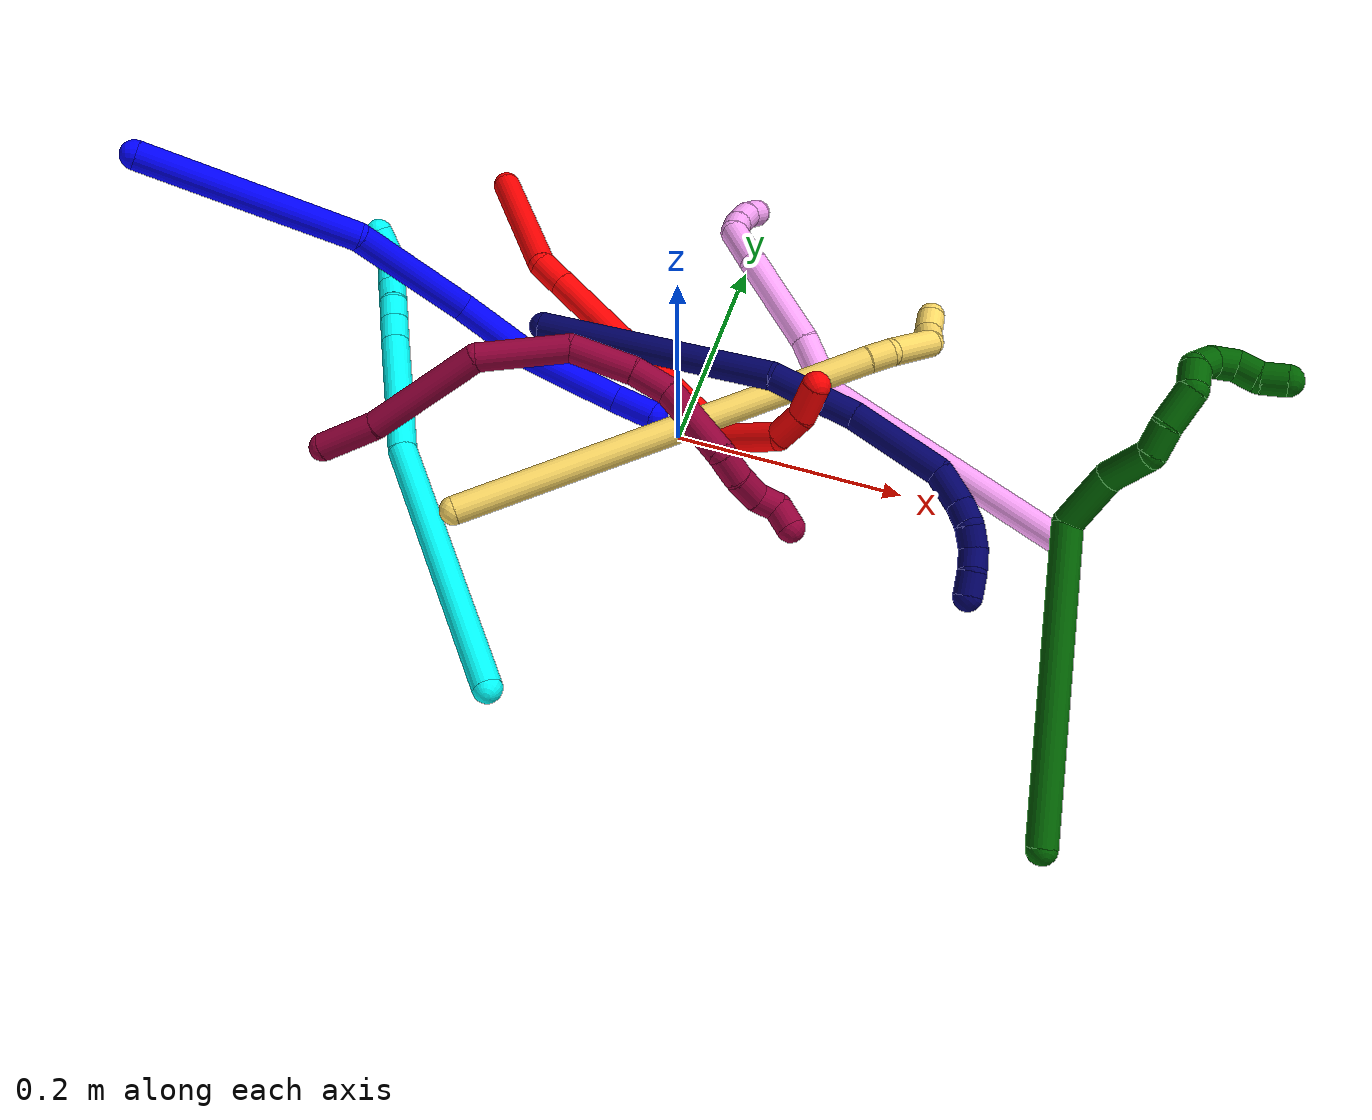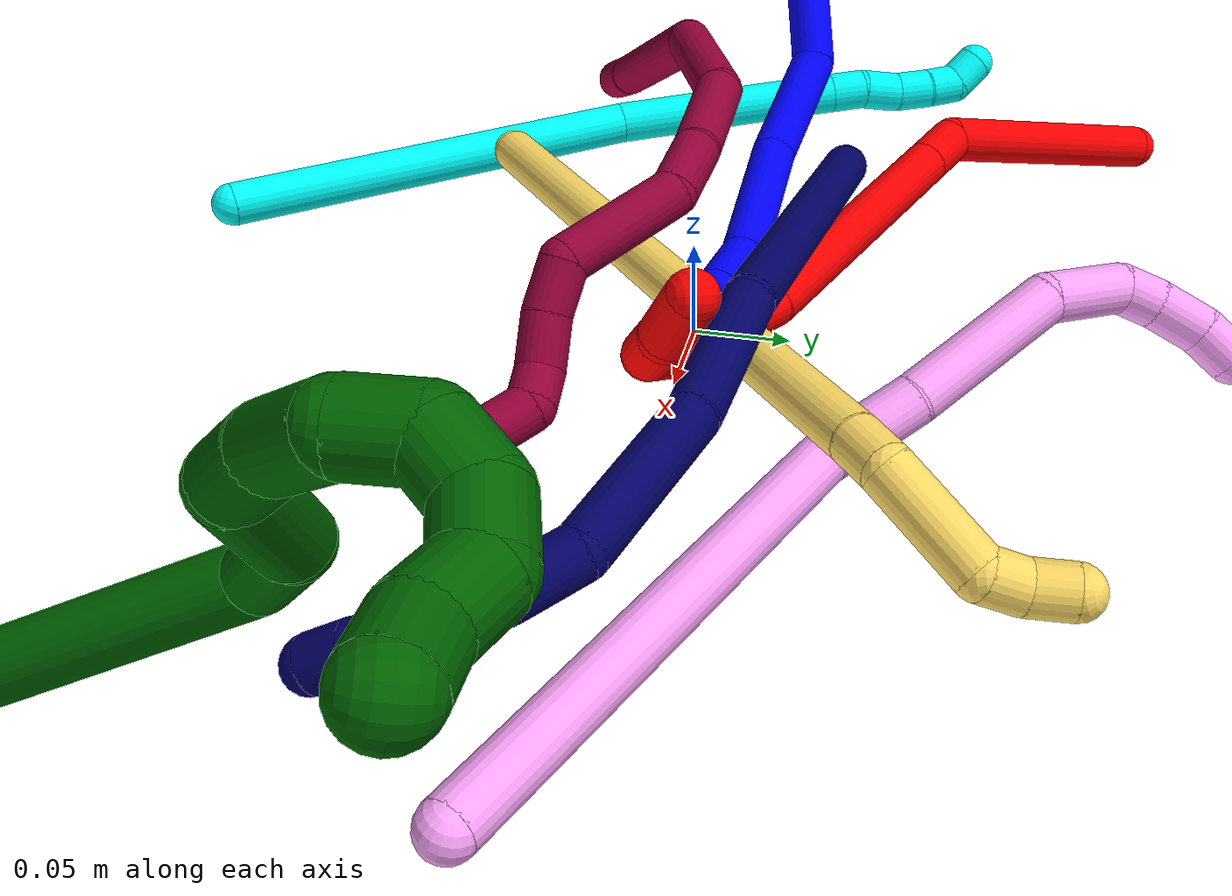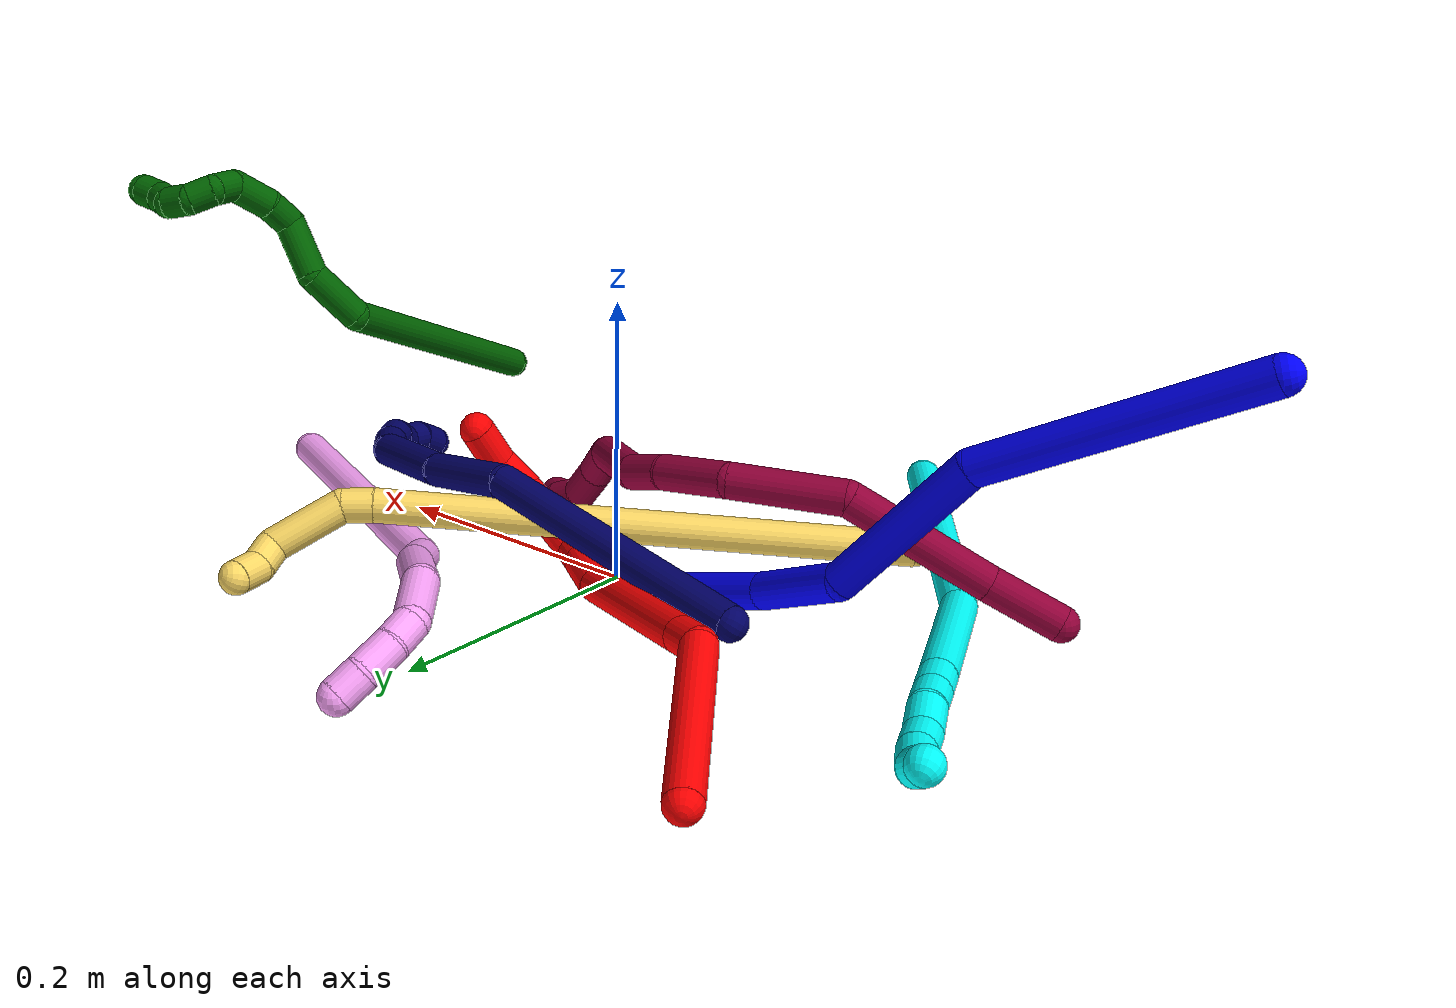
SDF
<sdf version="1.7">
 <world name="default">
  <plugin name="TubeGeneratorPlugin" filename="libtube_generator_plugin.so"/>
  <model name="photoneo_s_sensor">
   <static>1</static>
   <pose>0 0 2 1.57079 1.57079 3.14159</pose>
   <link name="link">
    <inertial><mass>0.1</mass></inertial>
    <sensor name="sensor" type="depth">
     <update_rate>30</update_rate>
     <camera>
      <horizontal_fov>1.22</horizontal_fov>
      <image><width>1920</width><height>1200</height><format>B8G8R8</format></image>
      <clip><near>0.1</near><far>4</far></clip>
      <depth_camera><output>points</output></depth_camera>
     </camera>
     <plugin name="camera_plugin" filename="libgazebo_ros_depth_camera.so">
      <baseline>0.2</baseline>
      <alwaysOn>1</alwaysOn>
      <updateRate>0.0</updateRate>
      <cameraName>camera_ir</cameraName>
      <imageTopicName>/camera/color/image_raw</imageTopicName>
      <cameraInfoTopicName>/camera/color/camera_info</cameraInfoTopicName>
      <depthImageTopicName>/camera/depth/image_raw</depthImageTopicName>
      <depthImageCameraInfoTopicName>/camera/depth/camera_info</depthImageCameraInfoTopicName>
      <pointCloudTopicName>/camera/depth/points</pointCloudTopicName>
      <frameName>fr_optical</frameName>
      <pointCloudCutoff>0.1</pointCloudCutoff>
      <pointCloudCutoffMax>2.0</pointCloudCutoffMax>
      <distortionK1>0</distortionK1>
      <distortionK2>0</distortionK2>
      <distortionK3>0</distortionK3>
      <distortionT1>0</distortionT1>
      <distortionT2>0</distortionT2>
      <CxPrime>0</CxPrime>
      <Cx>0</Cx>
      <Cy>0</Cy>
      <focalLength>0</focalLength>
      <hackBaseline>0</hackBaseline>
     </plugin>
    </sensor>
   </link>
  </model>
  <gravity>0 0 -9.8</gravity>
  <magnetic_field>6e-06 2.3e-05 -4.2e-05</magnetic_field>
  <atmosphere type="adiabatic"/>
  <physics name="default_physics" default="0" type="ode">
   <max_step_size>0.003</max_step_size>
   <real_time_factor>1</real_time_factor>
   <real_time_update_rate>1000</real_time_update_rate>
   <max_contacts>10000</max_contacts>
   <ode>
    <solver>
     <type>quick</type>
     <iters>100</iters>
     <sor>1.3</sor>
     <use_dynamic_moi_rescaling>0</use_dynamic_moi_rescaling>
    </solver>
    <constraints>
     <contact_max_correcting_vel>0</contact_max_correcting_vel>
     <contact_surface_layer>0.001</contact_surface_layer>
     <cfm>0</cfm>
     <erp>0.2</erp>
    </constraints>
   </ode>
  </physics>
  <scene><ambient>0.4 0.4 0.4 1</ambient><background>0.7 0.7 0.7 1</background><shadows>0</shadows></scene>
  <audio><device>default</device></audio>
  <spherical_coordinates>
   <surface_model>EARTH_WGS84</surface_model>
   <latitude_deg>0</latitude_deg>
   <longitude_deg>0</longitude_deg>
   <elevation>0</elevation>
   <heading_deg>0</heading_deg>
  </spherical_coordinates>
  <model name="bin">
   <static>1</static>
   <link name="bottom">
    <collision name="collision-bottom">
     <pose>0 0 -0.01 0 -0 0</pose>
     <geometry><box><size>0.8 0.6 0.02</size></box></geometry>
     <surface>
      <friction><ode><mu>100</mu><mu2>100</mu2></ode></friction>
      <contact><collide_bitmask>65535</collide_bitmask></contact>
     </surface>
    </collision>
   </link>
   <link name="west_wall">
    <collision name="collision-west_wall">
     <pose>-0.41 0 0.1 0 -0 0</pose>
     <geometry><box><size>0.02 0.6 0.2</size></box></geometry>
     <surface>
      <friction><ode><mu>100</mu><mu2>100</mu2></ode></friction>
      <contact><collide_bitmask>65535</collide_bitmask></contact>
     </surface>
    </collision>
   </link>
   <link name="east_wall">
    <collision name="collision-east_wall">
     <pose>0.41 0 0.1 0 -0 0</pose>
     <geometry><box><size>0.02 0.6 0.2</size></box></geometry>
     <surface>
      <friction><ode><mu>100</mu><mu2>100</mu2></ode></friction>
      <contact><collide_bitmask>65535</collide_bitmask></contact>
     </surface>
    </collision>
   </link>
   <link name="south_wall">
    <collision name="collision-south_wall">
     <pose>0 -0.31 0.1 0 -0 0</pose>
     <geometry><box><size>0.8 0.02 0.2</size></box></geometry>
     <surface>
      <friction><ode><mu>100</mu><mu2>100</mu2></ode></friction>
      <contact><collide_bitmask>65535</collide_bitmask></contact>
     </surface>
    </collision>
   </link>
   <link name="north_wall">
    <collision name="collision-north_wall">
     <pose>0 0.31 0.1 0 -0 0</pose>
     <geometry><box><size>0.8 0.02 0.2</size></box></geometry>
     <surface>
      <friction><ode><mu>100</mu><mu2>100</mu2></ode></friction>
      <contact><collide_bitmask>65535</collide_bitmask></contact>
     </surface>
    </collision>
   </link>
  </model>
  <model name="1">
   <static>0</static>
   <link name="1">
    <collision name="collision-cylinder-e_1_1_4">
     <pose>0.021118 -0.01757 -0.089955 2.9487 0.226455 1.73168</pose>
     <geometry><cylinder><radius>0.0125</radius><length>0.188113</length></cylinder></geometry>
     <surface>
      <friction><ode><mu>1.16</mu><mu2>1.16</mu2><slip1>0</slip1><slip2>0</slip2></ode></friction>
      <contact><ode><kp>1e+06</kp><kd>1</kd><max_vel>0</max_vel><min_depth>0.001</min_depth></ode></contact>
     </surface>
    </collision>
    <visual name="visual-cylinder-e_1_1_4">
     <pose>0.021118 -0.01757 -0.089955 2.9487 0.226455 1.73168</pose>
     <geometry><cylinder><radius>0.0125</radius><length>0.188113</length></cylinder></geometry>
     <material><ambient>0 0 1 1</ambient></material>
    </visual>
    <collision name="collision-cylinder-e_2_4_5">
     <pose>0.052404 -0.066819 -0.227627 2.55552 0.175704 0.56806</pose>
     <geometry><cylinder><radius>0.0125</radius><length>0.116341</length></cylinder></geometry>
     <surface>
      <friction><ode><mu>1.16</mu><mu2>1.16</mu2><slip1>0</slip1><slip2>0</slip2></ode></friction>
      <contact><ode><kp>1e+06</kp><kd>1</kd><max_vel>0</max_vel><min_depth>0.001</min_depth></ode></contact>
     </surface>
    </collision>
    <visual name="visual-cylinder-e_2_4_5">
     <pose>0.052404 -0.066819 -0.227627 2.55552 0.175704 0.56806</pose>
     <geometry><cylinder><radius>0.0125</radius><length>0.116341</length></cylinder></geometry>
     <material><ambient>0 0 1 1</ambient></material>
    </visual>
    <collision name="collision-cylinder-e_3_5_6">
     <pose>0.084147 -0.104144 -0.30551 2.95655 0.612726 2.57093</pose>
     <geometry><cylinder><radius>0.0125</radius><length>0.075028</length></cylinder></geometry>
     <surface>
      <friction><ode><mu>1.16</mu><mu2>1.16</mu2><slip1>0</slip1><slip2>0</slip2></ode></friction>
      <contact><ode><kp>1e+06</kp><kd>1</kd><max_vel>0</max_vel><min_depth>0.001</min_depth></ode></contact>
     </surface>
    </collision>
    <visual name="visual-cylinder-e_3_5_6">
     <pose>0.084147 -0.104144 -0.30551 2.95655 0.612726 2.57093</pose>
     <geometry><cylinder><radius>0.0125</radius><length>0.075028</length></cylinder></geometry>
     <material><ambient>0 0 1 1</ambient></material>
    </visual>
    <collision name="collision-cylinder-e_4_6_7">
     <pose>0.12523 -0.111084 -0.372111 3.1061 0.49133 3.00025</pose>
     <geometry><cylinder><radius>0.0125</radius><length>0.082699</length></cylinder></geometry>
     <surface>
      <friction><ode><mu>1.16</mu><mu2>1.16</mu2><slip1>0</slip1><slip2>0</slip2></ode></friction>
      <contact><ode><kp>1e+06</kp><kd>1</kd><max_vel>0</max_vel><min_depth>0.001</min_depth></ode></contact>
     </surface>
    </collision>
    <visual name="visual-cylinder-e_4_6_7">
     <pose>0.12523 -0.111084 -0.372111 3.1061 0.49133 3.00025</pose>
     <geometry><cylinder><radius>0.0125</radius><length>0.082699</length></cylinder></geometry>
     <material><ambient>0 0 1 1</ambient></material>
    </visual>
    <collision name="collision-cylinder-e_5_7_2">
     <pose>0.155771 -0.108053 -0.423282 -2.8561 0.622979 -2.30191</pose>
     <geometry><cylinder><radius>0.0125</radius><length>0.037819</length></cylinder></geometry>
     <surface>
      <friction><ode><mu>1.16</mu><mu2>1.16</mu2><slip1>0</slip1><slip2>0</slip2></ode></friction>
      <contact><ode><kp>1e+06</kp><kd>1</kd><max_vel>0</max_vel><min_depth>0.001</min_depth></ode></contact>
     </surface>
    </collision>
    <visual name="visual-cylinder-e_5_7_2">
     <pose>0.155771 -0.108053 -0.423282 -2.8561 0.622979 -2.30191</pose>
     <geometry><cylinder><radius>0.0125</radius><length>0.037819</length></cylinder></geometry>
     <material><ambient>0 0 1 1</ambient></material>
    </visual>
    <collision name="collision-sphere-2">
     <pose>0.166804 -0.103728 -0.438017 0 -0 0</pose>
     <geometry><sphere><radius>0.0125</radius></sphere></geometry>
     <surface>
      <friction><ode><mu>1.16</mu><mu2>1.16</mu2><slip1>0</slip1><slip2>0</slip2></ode></friction>
      <contact><ode><kp>1e+06</kp><kd>1</kd><max_vel>0</max_vel><min_depth>0.001</min_depth></ode></contact>
     </surface>
    </collision>
    <visual name="visual-sphere-2">
     <pose>0.166804 -0.103728 -0.438017 0 -0 0</pose>
     <geometry><sphere><radius>0.0125</radius></sphere></geometry>
     <material><ambient>0 0 1 1</ambient></material>
    </visual>
    <collision name="collision-sphere-7">
     <pose>0.144739 -0.112378 -0.408546 0 -0 0</pose>
     <geometry><sphere><radius>0.0125</radius></sphere></geometry>
     <surface>
      <friction><ode><mu>1.16</mu><mu2>1.16</mu2><slip1>0</slip1><slip2>0</slip2></ode></friction>
      <contact><ode><kp>1e+06</kp><kd>1</kd><max_vel>0</max_vel><min_depth>0.001</min_depth></ode></contact>
     </surface>
    </collision>
    <visual name="visual-sphere-7">
     <pose>0.144739 -0.112378 -0.408546 0 -0 0</pose>
     <geometry><sphere><radius>0.0125</radius></sphere></geometry>
     <material><ambient>0 0 1 1</ambient></material>
    </visual>
    <collision name="collision-sphere-6">
     <pose>0.105721 -0.10979 -0.335676 0 -0 0</pose>
     <geometry><sphere><radius>0.0125</radius></sphere></geometry>
     <surface>
      <friction><ode><mu>1.16</mu><mu2>1.16</mu2><slip1>0</slip1><slip2>0</slip2></ode></friction>
      <contact><ode><kp>1e+06</kp><kd>1</kd><max_vel>0</max_vel><min_depth>0.001</min_depth></ode></contact>
     </surface>
    </collision>
    <visual name="visual-sphere-6">
     <pose>0.105721 -0.10979 -0.335676 0 -0 0</pose>
     <geometry><sphere><radius>0.0125</radius></sphere></geometry>
     <material><ambient>0 0 1 1</ambient></material>
    </visual>
    <collision name="collision-sphere-5">
     <pose>0.062573 -0.098497 -0.275344 0 -0 0</pose>
     <geometry><sphere><radius>0.0125</radius></sphere></geometry>
     <surface>
      <friction><ode><mu>1.16</mu><mu2>1.16</mu2><slip1>0</slip1><slip2>0</slip2></ode></friction>
      <contact><ode><kp>1e+06</kp><kd>1</kd><max_vel>0</max_vel><min_depth>0.001</min_depth></ode></contact>
     </surface>
    </collision>
    <visual name="visual-sphere-5">
     <pose>0.062573 -0.098497 -0.275344 0 -0 0</pose>
     <geometry><sphere><radius>0.0125</radius></sphere></geometry>
     <material><ambient>0 0 1 1</ambient></material>
    </visual>
    <collision name="collision-sphere-1">
     <geometry><sphere><radius>0.0125</radius></sphere></geometry>
     <surface>
      <friction><ode><mu>1.16</mu><mu2>1.16</mu2><slip1>0</slip1><slip2>0</slip2></ode></friction>
      <contact><ode><kp>1e+06</kp><kd>1</kd><max_vel>0</max_vel><min_depth>0.001</min_depth></ode></contact>
     </surface>
    </collision>
    <visual name="visual-sphere-1">
     <geometry><sphere><radius>0.0125</radius></sphere></geometry>
     <material><ambient>0 0 1 1</ambient></material>
    </visual>
    <collision name="collision-sphere-4">
     <pose>0.042236 -0.03514 -0.17991 0 -0 0</pose>
     <geometry><sphere><radius>0.0125</radius></sphere></geometry>
     <surface>
      <friction><ode><mu>1.16</mu><mu2>1.16</mu2><slip1>0</slip1><slip2>0</slip2></ode></friction>
      <contact><ode><kp>1e+06</kp><kd>1</kd><max_vel>0</max_vel><min_depth>0.001</min_depth></ode></contact>
     </surface>
    </collision>
    <visual name="visual-sphere-4">
     <pose>0.042236 -0.03514 -0.17991 0 -0 0</pose>
     <geometry><sphere><radius>0.0125</radius></sphere></geometry>
     <material><ambient>0 0 1 1</ambient></material>
    </visual>
    <inertial>
     <pose>0.06526 -0.064331 -0.226214 0 -0 0</pose>
     <mass>0.5</mass>
     <inertia>
      <ixx>0.000597</ixx>
      <ixy>0</ixy>
      <ixz>0</ixz>
      <iyy>0.000736</iyy>
      <iyz>0</iyz>
      <izz>-4.8e-05</izz>
     </inertia>
    </inertial>
   </link>
   <pose>-0.447225 -0.032666 0.236665 1.31919 0.100345 -1.12625</pose>
  </model>
  <model name="2">
   <static>0</static>
   <link name="2">
    <collision name="collision-cylinder-e_1_1_4">
     <pose>-0.002177 -0.004907 -0.069579 3.07118 -0.031194 -0.833824</pose>
     <geometry><cylinder><radius>0.0125</radius><length>0.139572</length></cylinder></geometry>
     <surface>
      <friction><ode><mu>1.16</mu><mu2>1.16</mu2><slip1>0</slip1><slip2>0</slip2></ode></friction>
      <contact><ode><kp>1e+06</kp><kd>1</kd><max_vel>0</max_vel><min_depth>0.001</min_depth></ode></contact>
     </surface>
    </collision>
    <visual name="visual-cylinder-e_1_1_4">
     <pose>-0.002177 -0.004907 -0.069579 3.07118 -0.031194 -0.833824</pose>
     <geometry><cylinder><radius>0.0125</radius><length>0.139572</length></cylinder></geometry>
     <material><ambient>1 0 0 1</ambient></material>
    </visual>
    <collision name="collision-cylinder-e_2_4_5">
     <pose>0.003172 -0.010967 -0.150519 3.04055 0.582721 2.80753</pose>
     <geometry><cylinder><radius>0.0125</radius><length>0.02735</length></cylinder></geometry>
     <surface>
      <friction><ode><mu>1.16</mu><mu2>1.16</mu2><slip1>0</slip1><slip2>0</slip2></ode></friction>
      <contact><ode><kp>1e+06</kp><kd>1</kd><max_vel>0</max_vel><min_depth>0.001</min_depth></ode></contact>
     </surface>
    </collision>
    <visual name="visual-cylinder-e_2_4_5">
     <pose>0.003172 -0.010967 -0.150519 3.04055 0.582721 2.80753</pose>
     <geometry><cylinder><radius>0.0125</radius><length>0.02735</length></cylinder></geometry>
     <material><ambient>1 0 0 1</ambient></material>
    </visual>
    <collision name="collision-cylinder-e_3_5_6">
     <pose>0.051324 -0.018007 -0.223231 3.0459 0.582776 2.82495</pose>
     <geometry><cylinder><radius>0.0125</radius><length>0.147638</length></cylinder></geometry>
     <surface>
      <friction><ode><mu>1.16</mu><mu2>1.16</mu2><slip1>0</slip1><slip2>0</slip2></ode></friction>
      <contact><ode><kp>1e+06</kp><kd>1</kd><max_vel>0</max_vel><min_depth>0.001</min_depth></ode></contact>
     </surface>
    </collision>
    <visual name="visual-cylinder-e_3_5_6">
     <pose>0.051324 -0.018007 -0.223231 3.0459 0.582776 2.82495</pose>
     <geometry><cylinder><radius>0.0125</radius><length>0.147638</length></cylinder></geometry>
     <material><ambient>1 0 0 1</ambient></material>
    </visual>
    <collision name="collision-cylinder-e_4_6_7">
     <pose>0.099866 -0.02696 -0.304205 2.9867 0.379343 2.3733</pose>
     <geometry><cylinder><radius>0.0125</radius><length>0.042759</length></cylinder></geometry>
     <surface>
      <friction><ode><mu>1.16</mu><mu2>1.16</mu2><slip1>0</slip1><slip2>0</slip2></ode></friction>
      <contact><ode><kp>1e+06</kp><kd>1</kd><max_vel>0</max_vel><min_depth>0.001</min_depth></ode></contact>
     </surface>
    </collision>
    <visual name="visual-cylinder-e_4_6_7">
     <pose>0.099866 -0.02696 -0.304205 2.9867 0.379343 2.3733</pose>
     <geometry><cylinder><radius>0.0125</radius><length>0.042759</length></cylinder></geometry>
     <material><ambient>1 0 0 1</ambient></material>
    </visual>
    <collision name="collision-cylinder-e_5_7_8">
     <pose>0.112253 -0.03141 -0.334193 3.00867 0.403863 2.51289</pose>
     <geometry><cylinder><radius>0.0125</radius><length>0.022746</length></cylinder></geometry>
     <surface>
      <friction><ode><mu>1.16</mu><mu2>1.16</mu2><slip1>0</slip1><slip2>0</slip2></ode></friction>
      <contact><ode><kp>1e+06</kp><kd>1</kd><max_vel>0</max_vel><min_depth>0.001</min_depth></ode></contact>
     </surface>
    </collision>
    <visual name="visual-cylinder-e_5_7_8">
     <pose>0.112253 -0.03141 -0.334193 3.00867 0.403863 2.51289</pose>
     <geometry><cylinder><radius>0.0125</radius><length>0.022746</length></cylinder></geometry>
     <material><ambient>1 0 0 1</ambient></material>
    </visual>
    <collision name="collision-cylinder-e_6_8_9">
     <pose>0.123218 -0.055201 -0.363573 2.27452 0.217561 0.463379</pose>
     <geometry><cylinder><radius>0.0125</radius><length>0.06019</length></cylinder></geometry>
     <surface>
      <friction><ode><mu>1.16</mu><mu2>1.16</mu2><slip1>0</slip1><slip2>0</slip2></ode></friction>
      <contact><ode><kp>1e+06</kp><kd>1</kd><max_vel>0</max_vel><min_depth>0.001</min_depth></ode></contact>
     </surface>
    </collision>
    <visual name="visual-cylinder-e_6_8_9">
     <pose>0.123218 -0.055201 -0.363573 2.27452 0.217561 0.463379</pose>
     <geometry><cylinder><radius>0.0125</radius><length>0.06019</length></cylinder></geometry>
     <material><ambient>1 0 0 1</ambient></material>
    </visual>
    <collision name="collision-cylinder-e_7_9_10">
     <pose>0.130349 -0.091951 -0.384016 1.67002 0.044037 0.048636</pose>
     <geometry><cylinder><radius>0.0125</radius><length>0.02886</length></cylinder></geometry>
     <surface>
      <friction><ode><mu>1.16</mu><mu2>1.16</mu2><slip1>0</slip1><slip2>0</slip2></ode></friction>
      <contact><ode><kp>1e+06</kp><kd>1</kd><max_vel>0</max_vel><min_depth>0.001</min_depth></ode></contact>
     </surface>
    </collision>
    <visual name="visual-cylinder-e_7_9_10">
     <pose>0.130349 -0.091951 -0.384016 1.67002 0.044037 0.048636</pose>
     <geometry><cylinder><radius>0.0125</radius><length>0.02886</length></cylinder></geometry>
     <material><ambient>1 0 0 1</ambient></material>
    </visual>
    <collision name="collision-cylinder-e_8_10_2">
     <pose>0.127123 -0.121131 -0.38358 1.44581 -0.252788 -0.223277</pose>
     <geometry><cylinder><radius>0.0125</radius><length>0.030884</length></cylinder></geometry>
     <surface>
      <friction><ode><mu>1.16</mu><mu2>1.16</mu2><slip1>0</slip1><slip2>0</slip2></ode></friction>
      <contact><ode><kp>1e+06</kp><kd>1</kd><max_vel>0</max_vel><min_depth>0.001</min_depth></ode></contact>
     </surface>
    </collision>
    <visual name="visual-cylinder-e_8_10_2">
     <pose>0.127123 -0.121131 -0.38358 1.44581 -0.252788 -0.223277</pose>
     <geometry><cylinder><radius>0.0125</radius><length>0.030884</length></cylinder></geometry>
     <material><ambient>1 0 0 1</ambient></material>
    </visual>
    <collision name="collision-sphere-2">
     <pose>0.123261 -0.135965 -0.381716 0 -0 0</pose>
     <geometry><sphere><radius>0.0125</radius></sphere></geometry>
     <surface>
      <friction><ode><mu>1.16</mu><mu2>1.16</mu2><slip1>0</slip1><slip2>0</slip2></ode></friction>
      <contact><ode><kp>1e+06</kp><kd>1</kd><max_vel>0</max_vel><min_depth>0.001</min_depth></ode></contact>
     </surface>
    </collision>
    <visual name="visual-sphere-2">
     <pose>0.123261 -0.135965 -0.381716 0 -0 0</pose>
     <geometry><sphere><radius>0.0125</radius></sphere></geometry>
     <material><ambient>1 0 0 1</ambient></material>
    </visual>
    <collision name="collision-sphere-10">
     <pose>0.130985 -0.106297 -0.385444 0 -0 0</pose>
     <geometry><sphere><radius>0.0125</radius></sphere></geometry>
     <surface>
      <friction><ode><mu>1.16</mu><mu2>1.16</mu2><slip1>0</slip1><slip2>0</slip2></ode></friction>
      <contact><ode><kp>1e+06</kp><kd>1</kd><max_vel>0</max_vel><min_depth>0.001</min_depth></ode></contact>
     </surface>
    </collision>
    <visual name="visual-sphere-10">
     <pose>0.130985 -0.106297 -0.385444 0 -0 0</pose>
     <geometry><sphere><radius>0.0125</radius></sphere></geometry>
     <material><ambient>1 0 0 1</ambient></material>
    </visual>
    <collision name="collision-sphere-9">
     <pose>0.129714 -0.077606 -0.382588 0 -0 0</pose>
     <geometry><sphere><radius>0.0125</radius></sphere></geometry>
     <surface>
      <friction><ode><mu>1.16</mu><mu2>1.16</mu2><slip1>0</slip1><slip2>0</slip2></ode></friction>
      <contact><ode><kp>1e+06</kp><kd>1</kd><max_vel>0</max_vel><min_depth>0.001</min_depth></ode></contact>
     </surface>
    </collision>
    <visual name="visual-sphere-9">
     <pose>0.129714 -0.077606 -0.382588 0 -0 0</pose>
     <geometry><sphere><radius>0.0125</radius></sphere></geometry>
     <material><ambient>1 0 0 1</ambient></material>
    </visual>
    <collision name="collision-sphere-4">
     <pose>-0.004353 -0.009815 -0.139159 0 -0 0</pose>
     <geometry><sphere><radius>0.0125</radius></sphere></geometry>
     <surface>
      <friction><ode><mu>1.16</mu><mu2>1.16</mu2><slip1>0</slip1><slip2>0</slip2></ode></friction>
      <contact><ode><kp>1e+06</kp><kd>1</kd><max_vel>0</max_vel><min_depth>0.001</min_depth></ode></contact>
     </surface>
    </collision>
    <visual name="visual-sphere-4">
     <pose>-0.004353 -0.009815 -0.139159 0 -0 0</pose>
     <geometry><sphere><radius>0.0125</radius></sphere></geometry>
     <material><ambient>1 0 0 1</ambient></material>
    </visual>
    <collision name="collision-sphere-1">
     <geometry><sphere><radius>0.0125</radius></sphere></geometry>
     <surface>
      <friction><ode><mu>1.16</mu><mu2>1.16</mu2><slip1>0</slip1><slip2>0</slip2></ode></friction>
      <contact><ode><kp>1e+06</kp><kd>1</kd><max_vel>0</max_vel><min_depth>0.001</min_depth></ode></contact>
     </surface>
    </collision>
    <visual name="visual-sphere-1">
     <geometry><sphere><radius>0.0125</radius></sphere></geometry>
     <material><ambient>1 0 0 1</ambient></material>
    </visual>
    <collision name="collision-sphere-8">
     <pose>0.116722 -0.032796 -0.344559 0 -0 0</pose>
     <geometry><sphere><radius>0.0125</radius></sphere></geometry>
     <surface>
      <friction><ode><mu>1.16</mu><mu2>1.16</mu2><slip1>0</slip1><slip2>0</slip2></ode></friction>
      <contact><ode><kp>1e+06</kp><kd>1</kd><max_vel>0</max_vel><min_depth>0.001</min_depth></ode></contact>
     </surface>
    </collision>
    <visual name="visual-sphere-8">
     <pose>0.116722 -0.032796 -0.344559 0 -0 0</pose>
     <geometry><sphere><radius>0.0125</radius></sphere></geometry>
     <material><ambient>1 0 0 1</ambient></material>
    </visual>
    <collision name="collision-sphere-5">
     <pose>0.010698 -0.012118 -0.161879 0 -0 0</pose>
     <geometry><sphere><radius>0.0125</radius></sphere></geometry>
     <surface>
      <friction><ode><mu>1.16</mu><mu2>1.16</mu2><slip1>0</slip1><slip2>0</slip2></ode></friction>
      <contact><ode><kp>1e+06</kp><kd>1</kd><max_vel>0</max_vel><min_depth>0.001</min_depth></ode></contact>
     </surface>
    </collision>
    <visual name="visual-sphere-5">
     <pose>0.010698 -0.012118 -0.161879 0 -0 0</pose>
     <geometry><sphere><radius>0.0125</radius></sphere></geometry>
     <material><ambient>1 0 0 1</ambient></material>
    </visual>
    <collision name="collision-sphere-6">
     <pose>0.091949 -0.023897 -0.284584 0 -0 0</pose>
     <geometry><sphere><radius>0.0125</radius></sphere></geometry>
     <surface>
      <friction><ode><mu>1.16</mu><mu2>1.16</mu2><slip1>0</slip1><slip2>0</slip2></ode></friction>
      <contact><ode><kp>1e+06</kp><kd>1</kd><max_vel>0</max_vel><min_depth>0.001</min_depth></ode></contact>
     </surface>
    </collision>
    <visual name="visual-sphere-6">
     <pose>0.091949 -0.023897 -0.284584 0 -0 0</pose>
     <geometry><sphere><radius>0.0125</radius></sphere></geometry>
     <material><ambient>1 0 0 1</ambient></material>
    </visual>
    <collision name="collision-sphere-7">
     <pose>0.107783 -0.030024 -0.323827 0 -0 0</pose>
     <geometry><sphere><radius>0.0125</radius></sphere></geometry>
     <surface>
      <friction><ode><mu>1.16</mu><mu2>1.16</mu2><slip1>0</slip1><slip2>0</slip2></ode></friction>
      <contact><ode><kp>1e+06</kp><kd>1</kd><max_vel>0</max_vel><min_depth>0.001</min_depth></ode></contact>
     </surface>
    </collision>
    <visual name="visual-sphere-7">
     <pose>0.107783 -0.030024 -0.323827 0 -0 0</pose>
     <geometry><sphere><radius>0.0125</radius></sphere></geometry>
     <material><ambient>1 0 0 1</ambient></material>
    </visual>
    <inertial>
     <pose>0.058576 -0.030456 -0.224415 0 -0 0</pose>
     <mass>0.5</mass>
     <inertia>
      <ixx>-0.000122</ixx>
      <ixy>0</ixy>
      <ixz>0</ixz>
      <iyy>1.3e-05</iyy>
      <iyz>0</iyz>
      <izz>-0.000121</izz>
     </inertia>
    </inertial>
   </link>
   <pose>-0.248897 0.228508 0.011499 -1.77108 0.710709 0.469087</pose>
  </model>
  <model name="3">
   <static>0</static>
   <link name="3">
    <collision name="collision-cylinder-e_1_1_4">
     <pose>-0.060158 0.025633 0.105329 -0.238718 -0.506634 0.062074</pose>
     <geometry><cylinder><radius>0.0125</radius><length>0.247953</length></cylinder></geometry>
     <surface>
      <friction><ode><mu>1.16</mu><mu2>1.16</mu2><slip1>0</slip1><slip2>0</slip2></ode></friction>
      <contact><ode><kp>1e+06</kp><kd>1</kd><max_vel>0</max_vel><min_depth>0.001</min_depth></ode></contact>
     </surface>
    </collision>
    <visual name="visual-cylinder-e_1_1_4">
     <pose>-0.060158 0.025633 0.105329 -0.238718 -0.506634 0.062074</pose>
     <geometry><cylinder><radius>0.0125</radius><length>0.247953</length></cylinder></geometry>
     <material><ambient>0.003922 1 0.996078 1</ambient></material>
    </visual>
    <collision name="collision-cylinder-e_2_4_5">
     <pose>-0.147386 0.050523 0.262933 0.014205 -0.477766 -0.003459</pose>
     <geometry><cylinder><radius>0.0125</radius><length>0.117747</length></cylinder></geometry>
     <surface>
      <friction><ode><mu>1.16</mu><mu2>1.16</mu2><slip1>0</slip1><slip2>0</slip2></ode></friction>
      <contact><ode><kp>1e+06</kp><kd>1</kd><max_vel>0</max_vel><min_depth>0.001</min_depth></ode></contact>
     </surface>
    </collision>
    <visual name="visual-cylinder-e_2_4_5">
     <pose>-0.147386 0.050523 0.262933 0.014205 -0.477766 -0.003459</pose>
     <geometry><cylinder><radius>0.0125</radius><length>0.117747</length></cylinder></geometry>
     <material><ambient>0.003922 1 0.996078 1</ambient></material>
    </visual>
    <collision name="collision-cylinder-e_3_5_6">
     <pose>-0.179979 0.049492 0.326079 0.026469 -0.469958 -0.006337</pose>
     <geometry><cylinder><radius>0.0125</radius><length>0.024393</length></cylinder></geometry>
     <surface>
      <friction><ode><mu>1.16</mu><mu2>1.16</mu2><slip1>0</slip1><slip2>0</slip2></ode></friction>
      <contact><ode><kp>1e+06</kp><kd>1</kd><max_vel>0</max_vel><min_depth>0.001</min_depth></ode></contact>
     </surface>
    </collision>
    <visual name="visual-cylinder-e_3_5_6">
     <pose>-0.179979 0.049492 0.326079 0.026469 -0.469958 -0.006337</pose>
     <geometry><cylinder><radius>0.0125</radius><length>0.024393</length></cylinder></geometry>
     <material><ambient>0.003922 1 0.996078 1</ambient></material>
    </visual>
    <collision name="collision-cylinder-e_4_6_7">
     <pose>-0.190485 0.048939 0.346782 0.027047 -0.468985 -0.006462</pose>
     <geometry><cylinder><radius>0.0125</radius><length>0.022051</length></cylinder></geometry>
     <surface>
      <friction><ode><mu>1.16</mu><mu2>1.16</mu2><slip1>0</slip1><slip2>0</slip2></ode></friction>
      <contact><ode><kp>1e+06</kp><kd>1</kd><max_vel>0</max_vel><min_depth>0.001</min_depth></ode></contact>
     </surface>
    </collision>
    <visual name="visual-cylinder-e_4_6_7">
     <pose>-0.190485 0.048939 0.346782 0.027047 -0.468985 -0.006462</pose>
     <geometry><cylinder><radius>0.0125</radius><length>0.022051</length></cylinder></geometry>
     <material><ambient>0.003922 1 0.996078 1</ambient></material>
    </visual>
    <collision name="collision-cylinder-e_5_7_8">
     <pose>-0.198623 0.049869 0.368665 -0.098971 -0.254808 0.012688</pose>
     <geometry><cylinder><radius>0.0125</radius><length>0.025032</length></cylinder></geometry>
     <surface>
      <friction><ode><mu>1.16</mu><mu2>1.16</mu2><slip1>0</slip1><slip2>0</slip2></ode></friction>
      <contact><ode><kp>1e+06</kp><kd>1</kd><max_vel>0</max_vel><min_depth>0.001</min_depth></ode></contact>
     </surface>
    </collision>
    <visual name="visual-cylinder-e_5_7_8">
     <pose>-0.198623 0.049869 0.368665 -0.098971 -0.254808 0.012688</pose>
     <geometry><cylinder><radius>0.0125</radius><length>0.025032</length></cylinder></geometry>
     <material><ambient>0.003922 1 0.996078 1</ambient></material>
    </visual>
    <collision name="collision-cylinder-e_6_8_9">
     <pose>-0.206702 0.050778 0.390746 0.028707 -0.456233 -0.006665</pose>
     <geometry><cylinder><radius>0.0125</radius><length>0.022351</length></cylinder></geometry>
     <surface>
      <friction><ode><mu>1.16</mu><mu2>1.16</mu2><slip1>0</slip1><slip2>0</slip2></ode></friction>
      <contact><ode><kp>1e+06</kp><kd>1</kd><max_vel>0</max_vel><min_depth>0.001</min_depth></ode></contact>
     </surface>
    </collision>
    <visual name="visual-cylinder-e_6_8_9">
     <pose>-0.206702 0.050778 0.390746 0.028707 -0.456233 -0.006665</pose>
     <geometry><cylinder><radius>0.0125</radius><length>0.022351</length></cylinder></geometry>
     <material><ambient>0.003922 1 0.996078 1</ambient></material>
    </visual>
    <collision name="collision-cylinder-e_7_9_10">
     <pose>-0.216507 0.051498 0.409699 -0.112406 -0.497869 0.028603</pose>
     <geometry><cylinder><radius>0.0125</radius><length>0.020444</length></cylinder></geometry>
     <surface>
      <friction><ode><mu>1.16</mu><mu2>1.16</mu2><slip1>0</slip1><slip2>0</slip2></ode></friction>
      <contact><ode><kp>1e+06</kp><kd>1</kd><max_vel>0</max_vel><min_depth>0.001</min_depth></ode></contact>
     </surface>
    </collision>
    <visual name="visual-cylinder-e_7_9_10">
     <pose>-0.216507 0.051498 0.409699 -0.112406 -0.497869 0.028603</pose>
     <geometry><cylinder><radius>0.0125</radius><length>0.020444</length></cylinder></geometry>
     <material><ambient>0.003922 1 0.996078 1</ambient></material>
    </visual>
    <collision name="collision-cylinder-e_8_10_2">
     <pose>-0.23017 0.053626 0.423305 -0.235034 -1.06935 0.139607</pose>
     <geometry><cylinder><radius>0.0125</radius><length>0.020029</length></cylinder></geometry>
     <surface>
      <friction><ode><mu>1.16</mu><mu2>1.16</mu2><slip1>0</slip1><slip2>0</slip2></ode></friction>
      <contact><ode><kp>1e+06</kp><kd>1</kd><max_vel>0</max_vel><min_depth>0.001</min_depth></ode></contact>
     </surface>
    </collision>
    <visual name="visual-cylinder-e_8_10_2">
     <pose>-0.23017 0.053626 0.423305 -0.235034 -1.06935 0.139607</pose>
     <geometry><cylinder><radius>0.0125</radius><length>0.020029</length></cylinder></geometry>
     <material><ambient>0.003922 1 0.996078 1</ambient></material>
    </visual>
    <collision name="collision-sphere-2">
     <pose>-0.238952 0.054747 0.427987 0 -0 0</pose>
     <geometry><sphere><radius>0.0125</radius></sphere></geometry>
     <surface>
      <friction><ode><mu>1.16</mu><mu2>1.16</mu2><slip1>0</slip1><slip2>0</slip2></ode></friction>
      <contact><ode><kp>1e+06</kp><kd>1</kd><max_vel>0</max_vel><min_depth>0.001</min_depth></ode></contact>
     </surface>
    </collision>
    <visual name="visual-sphere-2">
     <pose>-0.238952 0.054747 0.427987 0 -0 0</pose>
     <geometry><sphere><radius>0.0125</radius></sphere></geometry>
     <material><ambient>0.003922 1 0.996078 1</ambient></material>
    </visual>
    <collision name="collision-sphere-10">
     <pose>-0.221389 0.052505 0.418624 0 -0 0</pose>
     <geometry><sphere><radius>0.0125</radius></sphere></geometry>
     <surface>
      <friction><ode><mu>1.16</mu><mu2>1.16</mu2><slip1>0</slip1><slip2>0</slip2></ode></friction>
      <contact><ode><kp>1e+06</kp><kd>1</kd><max_vel>0</max_vel><min_depth>0.001</min_depth></ode></contact>
     </surface>
    </collision>
    <visual name="visual-sphere-10">
     <pose>-0.221389 0.052505 0.418624 0 -0 0</pose>
     <geometry><sphere><radius>0.0125</radius></sphere></geometry>
     <material><ambient>0.003922 1 0.996078 1</ambient></material>
    </visual>
    <collision name="collision-sphere-9">
     <pose>-0.211625 0.05049 0.400775 0 -0 0</pose>
     <geometry><sphere><radius>0.0125</radius></sphere></geometry>
     <surface>
      <friction><ode><mu>1.16</mu><mu2>1.16</mu2><slip1>0</slip1><slip2>0</slip2></ode></friction>
      <contact><ode><kp>1e+06</kp><kd>1</kd><max_vel>0</max_vel><min_depth>0.001</min_depth></ode></contact>
     </surface>
    </collision>
    <visual name="visual-sphere-9">
     <pose>-0.211625 0.05049 0.400775 0 -0 0</pose>
     <geometry><sphere><radius>0.0125</radius></sphere></geometry>
     <material><ambient>0.003922 1 0.996078 1</ambient></material>
    </visual>
    <collision name="collision-sphere-4">
     <pose>-0.120316 0.051265 0.210657 0 -0 0</pose>
     <geometry><sphere><radius>0.0125</radius></sphere></geometry>
     <surface>
      <friction><ode><mu>1.16</mu><mu2>1.16</mu2><slip1>0</slip1><slip2>0</slip2></ode></friction>
      <contact><ode><kp>1e+06</kp><kd>1</kd><max_vel>0</max_vel><min_depth>0.001</min_depth></ode></contact>
     </surface>
    </collision>
    <visual name="visual-sphere-4">
     <pose>-0.120316 0.051265 0.210657 0 -0 0</pose>
     <geometry><sphere><radius>0.0125</radius></sphere></geometry>
     <material><ambient>0.003922 1 0.996078 1</ambient></material>
    </visual>
    <collision name="collision-sphere-1">
     <geometry><sphere><radius>0.0125</radius></sphere></geometry>
     <surface>
      <friction><ode><mu>1.16</mu><mu2>1.16</mu2><slip1>0</slip1><slip2>0</slip2></ode></friction>
      <contact><ode><kp>1e+06</kp><kd>1</kd><max_vel>0</max_vel><min_depth>0.001</min_depth></ode></contact>
     </surface>
    </collision>
    <visual name="visual-sphere-1">
     <geometry><sphere><radius>0.0125</radius></sphere></geometry>
     <material><ambient>0.003922 1 0.996078 1</ambient></material>
    </visual>
    <collision name="collision-sphere-8">
     <pose>-0.201778 0.051066 0.380718 0 -0 0</pose>
     <geometry><sphere><radius>0.0125</radius></sphere></geometry>
     <surface>
      <friction><ode><mu>1.16</mu><mu2>1.16</mu2><slip1>0</slip1><slip2>0</slip2></ode></friction>
      <contact><ode><kp>1e+06</kp><kd>1</kd><max_vel>0</max_vel><min_depth>0.001</min_depth></ode></contact>
     </surface>
    </collision>
    <visual name="visual-sphere-8">
     <pose>-0.201778 0.051066 0.380718 0 -0 0</pose>
     <geometry><sphere><radius>0.0125</radius></sphere></geometry>
     <material><ambient>0.003922 1 0.996078 1</ambient></material>
    </visual>
    <collision name="collision-sphere-5">
     <pose>-0.174455 0.04978 0.315209 0 -0 0</pose>
     <geometry><sphere><radius>0.0125</radius></sphere></geometry>
     <surface>
      <friction><ode><mu>1.16</mu><mu2>1.16</mu2><slip1>0</slip1><slip2>0</slip2></ode></friction>
      <contact><ode><kp>1e+06</kp><kd>1</kd><max_vel>0</max_vel><min_depth>0.001</min_depth></ode></contact>
     </surface>
    </collision>
    <visual name="visual-sphere-5">
     <pose>-0.174455 0.04978 0.315209 0 -0 0</pose>
     <geometry><sphere><radius>0.0125</radius></sphere></geometry>
     <material><ambient>0.003922 1 0.996078 1</ambient></material>
    </visual>
    <collision name="collision-sphere-6">
     <pose>-0.185502 0.049205 0.33695 0 -0 0</pose>
     <geometry><sphere><radius>0.0125</radius></sphere></geometry>
     <surface>
      <friction><ode><mu>1.16</mu><mu2>1.16</mu2><slip1>0</slip1><slip2>0</slip2></ode></friction>
      <contact><ode><kp>1e+06</kp><kd>1</kd><max_vel>0</max_vel><min_depth>0.001</min_depth></ode></contact>
     </surface>
    </collision>
    <visual name="visual-sphere-6">
     <pose>-0.185502 0.049205 0.33695 0 -0 0</pose>
     <geometry><sphere><radius>0.0125</radius></sphere></geometry>
     <material><ambient>0.003922 1 0.996078 1</ambient></material>
    </visual>
    <collision name="collision-sphere-7">
     <pose>-0.195469 0.048673 0.356613 0 -0 0</pose>
     <geometry><sphere><radius>0.0125</radius></sphere></geometry>
     <surface>
      <friction><ode><mu>1.16</mu><mu2>1.16</mu2><slip1>0</slip1><slip2>0</slip2></ode></friction>
      <contact><ode><kp>1e+06</kp><kd>1</kd><max_vel>0</max_vel><min_depth>0.001</min_depth></ode></contact>
     </surface>
    </collision>
    <visual name="visual-sphere-7">
     <pose>-0.195469 0.048673 0.356613 0 -0 0</pose>
     <geometry><sphere><radius>0.0125</radius></sphere></geometry>
     <material><ambient>0.003922 1 0.996078 1</ambient></material>
    </visual>
    <inertial>
     <pose>-0.118979 0.038202 0.214987 0 -0 0</pose>
     <mass>0.5</mass>
     <inertia>
      <ixx>0.001302</ixx>
      <ixy>0</ixy>
      <ixz>0</ixz>
      <iyy>0.001475</iyy>
      <iyz>0</iyz>
      <izz>0.000461</izz>
     </inertia>
    </inertial>
   </link>
   <pose>-0.064072 -0.287978 0.011492 -2.43327 1.01416 -0.487502</pose>
  </model>
  <model name="4">
   <static>0</static>
   <link name="4">
    <collision name="collision-cylinder-e_1_1_4">
     <pose>-0.109731 0.050428 0.027769 -1.06743 -1.08764 0.68631</pose>
     <geometry><cylinder><radius>0.0125</radius><length>0.24783</length></cylinder></geometry>
     <surface>
      <friction><ode><mu>1.16</mu><mu2>1.16</mu2><slip1>0</slip1><slip2>0</slip2></ode></friction>
      <contact><ode><kp>1e+06</kp><kd>1</kd><max_vel>0</max_vel><min_depth>0.001</min_depth></ode></contact>
     </surface>
    </collision>
    <visual name="visual-cylinder-e_1_1_4">
     <pose>-0.109731 0.050428 0.027769 -1.06743 -1.08764 0.68631</pose>
     <geometry><cylinder><radius>0.0125</radius><length>0.24783</length></cylinder></geometry>
     <material><ambient>1 0.65098 0.996078 1</ambient></material>
    </visual>
    <collision name="collision-cylinder-e_2_4_5">
     <pose>-0.233014 0.116662 0.069973 -0.830754 -0.564416 0.254375</pose>
     <geometry><cylinder><radius>0.0125</radius><length>0.050669</length></cylinder></geometry>
     <surface>
      <friction><ode><mu>1.16</mu><mu2>1.16</mu2><slip1>0</slip1><slip2>0</slip2></ode></friction>
      <contact><ode><kp>1e+06</kp><kd>1</kd><max_vel>0</max_vel><min_depth>0.001</min_depth></ode></contact>
     </surface>
    </collision>
    <visual name="visual-cylinder-e_2_4_5">
     <pose>-0.233014 0.116662 0.069973 -0.830754 -0.564416 0.254375</pose>
     <geometry><cylinder><radius>0.0125</radius><length>0.050669</length></cylinder></geometry>
     <material><ambient>1 0.65098 0.996078 1</ambient></material>
    </visual>
    <collision name="collision-cylinder-e_3_5_6">
     <pose>-0.27541 0.15689 0.106866 -0.827241 -0.715623 0.325346</pose>
     <geometry><cylinder><radius>0.0125</radius><length>0.087928</length></cylinder></geometry>
     <surface>
      <friction><ode><mu>1.16</mu><mu2>1.16</mu2><slip1>0</slip1><slip2>0</slip2></ode></friction>
      <contact><ode><kp>1e+06</kp><kd>1</kd><max_vel>0</max_vel><min_depth>0.001</min_depth></ode></contact>
     </surface>
    </collision>
    <visual name="visual-cylinder-e_3_5_6">
     <pose>-0.27541 0.15689 0.106866 -0.827241 -0.715623 0.325346</pose>
     <geometry><cylinder><radius>0.0125</radius><length>0.087928</length></cylinder></geometry>
     <material><ambient>1 0.65098 0.996078 1</ambient></material>
    </visual>
    <collision name="collision-cylinder-e_4_6_7">
     <pose>-0.317611 0.200037 0.133085 -1.37262 -0.610279 0.505012</pose>
     <geometry><cylinder><radius>0.0125</radius><length>0.046611</length></cylinder></geometry>
     <surface>
      <friction><ode><mu>1.16</mu><mu2>1.16</mu2><slip1>0</slip1><slip2>0</slip2></ode></friction>
      <contact><ode><kp>1e+06</kp><kd>1</kd><max_vel>0</max_vel><min_depth>0.001</min_depth></ode></contact>
     </surface>
    </collision>
    <visual name="visual-cylinder-e_4_6_7">
     <pose>-0.317611 0.200037 0.133085 -1.37262 -0.610279 0.505012</pose>
     <geometry><cylinder><radius>0.0125</radius><length>0.046611</length></cylinder></geometry>
     <material><ambient>1 0.65098 0.996078 1</ambient></material>
    </visual>
    <collision name="collision-cylinder-e_5_7_8">
     <pose>-0.331608 0.228733 0.135888 -1.66654 -0.06395 0.070381</pose>
     <geometry><cylinder><radius>0.0125</radius><length>0.020074</length></cylinder></geometry>
     <surface>
      <friction><ode><mu>1.16</mu><mu2>1.16</mu2><slip1>0</slip1><slip2>0</slip2></ode></friction>
      <contact><ode><kp>1e+06</kp><kd>1</kd><max_vel>0</max_vel><min_depth>0.001</min_depth></ode></contact>
     </surface>
    </collision>
    <visual name="visual-cylinder-e_5_7_8">
     <pose>-0.331608 0.228733 0.135888 -1.66654 -0.06395 0.070381</pose>
     <geometry><cylinder><radius>0.0125</radius><length>0.020074</length></cylinder></geometry>
     <material><ambient>1 0.65098 0.996078 1</ambient></material>
    </visual>
    <collision name="collision-cylinder-e_6_8_9">
     <pose>-0.331048 0.251577 0.132748 -1.73872 0.091818 -0.108663</pose>
     <geometry><cylinder><radius>0.0125</radius><length>0.026225</length></cylinder></geometry>
     <surface>
      <friction><ode><mu>1.16</mu><mu2>1.16</mu2><slip1>0</slip1><slip2>0</slip2></ode></friction>
      <contact><ode><kp>1e+06</kp><kd>1</kd><max_vel>0</max_vel><min_depth>0.001</min_depth></ode></contact>
     </surface>
    </collision>
    <visual name="visual-cylinder-e_6_8_9">
     <pose>-0.331048 0.251577 0.132748 -1.73872 0.091818 -0.108663</pose>
     <geometry><cylinder><radius>0.0125</radius><length>0.026225</length></cylinder></geometry>
     <material><ambient>1 0.65098 0.996078 1</ambient></material>
    </visual>
    <collision name="collision-cylinder-e_7_9_2">
     <pose>-0.327222 0.273821 0.127094 -1.92563 0.256754 -0.366815</pose>
     <geometry><cylinder><radius>0.0125</radius><length>0.020662</length></cylinder></geometry>
     <surface>
      <friction><ode><mu>1.16</mu><mu2>1.16</mu2><slip1>0</slip1><slip2>0</slip2></ode></friction>
      <contact><ode><kp>1e+06</kp><kd>1</kd><max_vel>0</max_vel><min_depth>0.001</min_depth></ode></contact>
     </surface>
    </collision>
    <visual name="visual-cylinder-e_7_9_2">
     <pose>-0.327222 0.273821 0.127094 -1.92563 0.256754 -0.366815</pose>
     <geometry><cylinder><radius>0.0125</radius><length>0.020662</length></cylinder></geometry>
     <material><ambient>1 0.65098 0.996078 1</ambient></material>
    </visual>
    <collision name="collision-sphere-2">
     <pose>-0.324598 0.28319 0.123622 0 -0 0</pose>
     <geometry><sphere><radius>0.0125</radius></sphere></geometry>
     <surface>
      <friction><ode><mu>1.16</mu><mu2>1.16</mu2><slip1>0</slip1><slip2>0</slip2></ode></friction>
      <contact><ode><kp>1e+06</kp><kd>1</kd><max_vel>0</max_vel><min_depth>0.001</min_depth></ode></contact>
     </surface>
    </collision>
    <visual name="visual-sphere-2">
     <pose>-0.324598 0.28319 0.123622 0 -0 0</pose>
     <geometry><sphere><radius>0.0125</radius></sphere></geometry>
     <material><ambient>1 0.65098 0.996078 1</ambient></material>
    </visual>
    <collision name="collision-sphere-9">
     <pose>-0.329845 0.264451 0.130565 0 -0 0</pose>
     <geometry><sphere><radius>0.0125</radius></sphere></geometry>
     <surface>
      <friction><ode><mu>1.16</mu><mu2>1.16</mu2><slip1>0</slip1><slip2>0</slip2></ode></friction>
      <contact><ode><kp>1e+06</kp><kd>1</kd><max_vel>0</max_vel><min_depth>0.001</min_depth></ode></contact>
     </surface>
    </collision>
    <visual name="visual-sphere-9">
     <pose>-0.329845 0.264451 0.130565 0 -0 0</pose>
     <geometry><sphere><radius>0.0125</radius></sphere></geometry>
     <material><ambient>1 0.65098 0.996078 1</ambient></material>
    </visual>
    <collision name="collision-sphere-4">
     <pose>-0.219462 0.100855 0.055539 0 -0 0</pose>
     <geometry><sphere><radius>0.0125</radius></sphere></geometry>
     <surface>
      <friction><ode><mu>1.16</mu><mu2>1.16</mu2><slip1>0</slip1><slip2>0</slip2></ode></friction>
      <contact><ode><kp>1e+06</kp><kd>1</kd><max_vel>0</max_vel><min_depth>0.001</min_depth></ode></contact>
     </surface>
    </collision>
    <visual name="visual-sphere-4">
     <pose>-0.219462 0.100855 0.055539 0 -0 0</pose>
     <geometry><sphere><radius>0.0125</radius></sphere></geometry>
     <material><ambient>1 0.65098 0.996078 1</ambient></material>
    </visual>
    <collision name="collision-sphere-1">
     <geometry><sphere><radius>0.0125</radius></sphere></geometry>
     <surface>
      <friction><ode><mu>1.16</mu><mu2>1.16</mu2><slip1>0</slip1><slip2>0</slip2></ode></friction>
      <contact><ode><kp>1e+06</kp><kd>1</kd><max_vel>0</max_vel><min_depth>0.001</min_depth></ode></contact>
     </surface>
    </collision>
    <visual name="visual-sphere-1">
     <geometry><sphere><radius>0.0125</radius></sphere></geometry>
     <material><ambient>1 0.65098 0.996078 1</ambient></material>
    </visual>
    <collision name="collision-sphere-8">
     <pose>-0.33225 0.238703 0.13493 0 -0 0</pose>
     <geometry><sphere><radius>0.0125</radius></sphere></geometry>
     <surface>
      <friction><ode><mu>1.16</mu><mu2>1.16</mu2><slip1>0</slip1><slip2>0</slip2></ode></friction>
      <contact><ode><kp>1e+06</kp><kd>1</kd><max_vel>0</max_vel><min_depth>0.001</min_depth></ode></contact>
     </surface>
    </collision>
    <visual name="visual-sphere-8">
     <pose>-0.33225 0.238703 0.13493 0 -0 0</pose>
     <geometry><sphere><radius>0.0125</radius></sphere></geometry>
     <material><ambient>1 0.65098 0.996078 1</ambient></material>
    </visual>
    <collision name="collision-sphere-5">
     <pose>-0.246566 0.132468 0.084406 0 -0 0</pose>
     <geometry><sphere><radius>0.0125</radius></sphere></geometry>
     <surface>
      <friction><ode><mu>1.16</mu><mu2>1.16</mu2><slip1>0</slip1><slip2>0</slip2></ode></friction>
      <contact><ode><kp>1e+06</kp><kd>1</kd><max_vel>0</max_vel><min_depth>0.001</min_depth></ode></contact>
     </surface>
    </collision>
    <visual name="visual-sphere-5">
     <pose>-0.246566 0.132468 0.084406 0 -0 0</pose>
     <geometry><sphere><radius>0.0125</radius></sphere></geometry>
     <material><ambient>1 0.65098 0.996078 1</ambient></material>
    </visual>
    <collision name="collision-sphere-6">
     <pose>-0.304254 0.181312 0.129325 0 -0 0</pose>
     <geometry><sphere><radius>0.0125</radius></sphere></geometry>
     <surface>
      <friction><ode><mu>1.16</mu><mu2>1.16</mu2><slip1>0</slip1><slip2>0</slip2></ode></friction>
      <contact><ode><kp>1e+06</kp><kd>1</kd><max_vel>0</max_vel><min_depth>0.001</min_depth></ode></contact>
     </surface>
    </collision>
    <visual name="visual-sphere-6">
     <pose>-0.304254 0.181312 0.129325 0 -0 0</pose>
     <geometry><sphere><radius>0.0125</radius></sphere></geometry>
     <material><ambient>1 0.65098 0.996078 1</ambient></material>
    </visual>
    <collision name="collision-sphere-7">
     <pose>-0.330967 0.218762 0.136845 0 -0 0</pose>
     <geometry><sphere><radius>0.0125</radius></sphere></geometry>
     <surface>
      <friction><ode><mu>1.16</mu><mu2>1.16</mu2><slip1>0</slip1><slip2>0</slip2></ode></friction>
      <contact><ode><kp>1e+06</kp><kd>1</kd><max_vel>0</max_vel><min_depth>0.001</min_depth></ode></contact>
     </surface>
    </collision>
    <visual name="visual-sphere-7">
     <pose>-0.330967 0.218762 0.136845 0 -0 0</pose>
     <geometry><sphere><radius>0.0125</radius></sphere></geometry>
     <material><ambient>1 0.65098 0.996078 1</ambient></material>
    </visual>
    <inertial>
     <pose>-0.200243 0.116749 0.069725 0 -0 0</pose>
     <mass>0.5</mass>
     <inertia>
      <ixx>0.000897</ixx>
      <ixy>0</ixy>
      <ixz>0</ixz>
      <iyy>0.001585</iyy>
      <iyz>0</iyz>
      <izz>0.000618</izz>
     </inertia>
    </inertial>
   </link>
   <pose>0.339693 -0.013008 0.011499 -0.300064 -0.105533 0.07778</pose>
  </model>
  <model name="5">
   <static>0</static>
   <link name="5">
    <collision name="collision-cylinder-e_1_1_4">
     <pose>0.073164 0.084678 0.153525 -0.504041 0.395327 -0.10305</pose>
     <geometry><cylinder><radius>0.0125</radius><length>0.379965</length></cylinder></geometry>
     <surface>
      <friction><ode><mu>1.16</mu><mu2>1.16</mu2><slip1>0</slip1><slip2>0</slip2></ode></friction>
      <contact><ode><kp>1e+06</kp><kd>1</kd><max_vel>0</max_vel><min_depth>0.001</min_depth></ode></contact>
     </surface>
    </collision>
    <visual name="visual-cylinder-e_1_1_4">
     <pose>0.073164 0.084678 0.153525 -0.504041 0.395327 -0.10305</pose>
     <geometry><cylinder><radius>0.0125</radius><length>0.379965</length></cylinder></geometry>
     <material><ambient>1 0.858824 0.4 1</ambient></material>
    </visual>
    <collision name="collision-cylinder-e_2_4_5">
     <pose>0.150005 0.175181 0.315881 -0.583015 0.334533 -0.101239</pose>
     <geometry><cylinder><radius>0.0125</radius><length>0.0224</length></cylinder></geometry>
     <surface>
      <friction><ode><mu>1.16</mu><mu2>1.16</mu2><slip1>0</slip1><slip2>0</slip2></ode></friction>
      <contact><ode><kp>1e+06</kp><kd>1</kd><max_vel>0</max_vel><min_depth>0.001</min_depth></ode></contact>
     </surface>
    </collision>
    <visual name="visual-cylinder-e_2_4_5">
     <pose>0.150005 0.175181 0.315881 -0.583015 0.334533 -0.101239</pose>
     <geometry><cylinder><radius>0.0125</radius><length>0.0224</length></cylinder></geometry>
     <material><ambient>1 0.858824 0.4 1</ambient></material>
    </visual>
    <collision name="collision-cylinder-e_3_5_6">
     <pose>0.150873 0.202131 0.342721 -0.864899 -0.10087 0.046592</pose>
     <geometry><cylinder><radius>0.0125</radius><length>0.055803</length></cylinder></geometry>
     <surface>
      <friction><ode><mu>1.16</mu><mu2>1.16</mu2><slip1>0</slip1><slip2>0</slip2></ode></friction>
      <contact><ode><kp>1e+06</kp><kd>1</kd><max_vel>0</max_vel><min_depth>0.001</min_depth></ode></contact>
     </surface>
    </collision>
    <visual name="visual-cylinder-e_3_5_6">
     <pose>0.150873 0.202131 0.342721 -0.864899 -0.10087 0.046592</pose>
     <geometry><cylinder><radius>0.0125</radius><length>0.055803</length></cylinder></geometry>
     <material><ambient>1 0.858824 0.4 1</ambient></material>
    </visual>
    <collision name="collision-cylinder-e_4_6_7">
     <pose>0.140416 0.227105 0.366608 -0.579575 -0.827679 0.260442</pose>
     <geometry><cylinder><radius>0.0125</radius><length>0.020771</length></cylinder></geometry>
     <surface>
      <friction><ode><mu>1.16</mu><mu2>1.16</mu2><slip1>0</slip1><slip2>0</slip2></ode></friction>
      <contact><ode><kp>1e+06</kp><kd>1</kd><max_vel>0</max_vel><min_depth>0.001</min_depth></ode></contact>
     </surface>
    </collision>
    <visual name="visual-cylinder-e_4_6_7">
     <pose>0.140416 0.227105 0.366608 -0.579575 -0.827679 0.260442</pose>
     <geometry><cylinder><radius>0.0125</radius><length>0.020771</length></cylinder></geometry>
     <material><ambient>1 0.858824 0.4 1</ambient></material>
    </visual>
    <collision name="collision-cylinder-e_5_7_2">
     <pose>0.127298 0.232538 0.381345 -0.17697 -0.546233 0.049692</pose>
     <geometry><cylinder><radius>0.0125</radius><length>0.021061</length></cylinder></geometry>
     <surface>
      <friction><ode><mu>1.16</mu><mu2>1.16</mu2><slip1>0</slip1><slip2>0</slip2></ode></friction>
      <contact><ode><kp>1e+06</kp><kd>1</kd><max_vel>0</max_vel><min_depth>0.001</min_depth></ode></contact>
     </surface>
    </collision>
    <visual name="visual-cylinder-e_5_7_2">
     <pose>0.127298 0.232538 0.381345 -0.17697 -0.546233 0.049692</pose>
     <geometry><cylinder><radius>0.0125</radius><length>0.021061</length></cylinder></geometry>
     <material><ambient>1 0.858824 0.4 1</ambient></material>
    </visual>
    <collision name="collision-sphere-2">
     <pose>0.121827 0.234122 0.390203 0 -0 0</pose>
     <geometry><sphere><radius>0.0125</radius></sphere></geometry>
     <surface>
      <friction><ode><mu>1.16</mu><mu2>1.16</mu2><slip1>0</slip1><slip2>0</slip2></ode></friction>
      <contact><ode><kp>1e+06</kp><kd>1</kd><max_vel>0</max_vel><min_depth>0.001</min_depth></ode></contact>
     </surface>
    </collision>
    <visual name="visual-sphere-2">
     <pose>0.121827 0.234122 0.390203 0 -0 0</pose>
     <geometry><sphere><radius>0.0125</radius></sphere></geometry>
     <material><ambient>1 0.858824 0.4 1</ambient></material>
    </visual>
    <collision name="collision-sphere-7">
     <pose>0.132768 0.230954 0.372487 0 -0 0</pose>
     <geometry><sphere><radius>0.0125</radius></sphere></geometry>
     <surface>
      <friction><ode><mu>1.16</mu><mu2>1.16</mu2><slip1>0</slip1><slip2>0</slip2></ode></friction>
      <contact><ode><kp>1e+06</kp><kd>1</kd><max_vel>0</max_vel><min_depth>0.001</min_depth></ode></contact>
     </surface>
    </collision>
    <visual name="visual-sphere-7">
     <pose>0.132768 0.230954 0.372487 0 -0 0</pose>
     <geometry><sphere><radius>0.0125</radius></sphere></geometry>
     <material><ambient>1 0.858824 0.4 1</ambient></material>
    </visual>
    <collision name="collision-sphere-6">
     <pose>0.148063 0.223257 0.360729 0 -0 0</pose>
     <geometry><sphere><radius>0.0125</radius></sphere></geometry>
     <surface>
      <friction><ode><mu>1.16</mu><mu2>1.16</mu2><slip1>0</slip1><slip2>0</slip2></ode></friction>
      <contact><ode><kp>1e+06</kp><kd>1</kd><max_vel>0</max_vel><min_depth>0.001</min_depth></ode></contact>
     </surface>
    </collision>
    <visual name="visual-sphere-6">
     <pose>0.148063 0.223257 0.360729 0 -0 0</pose>
     <geometry><sphere><radius>0.0125</radius></sphere></geometry>
     <material><ambient>1 0.858824 0.4 1</ambient></material>
    </visual>
    <collision name="collision-sphere-5">
     <pose>0.153683 0.181005 0.324712 0 -0 0</pose>
     <geometry><sphere><radius>0.0125</radius></sphere></geometry>
     <surface>
      <friction><ode><mu>1.16</mu><mu2>1.16</mu2><slip1>0</slip1><slip2>0</slip2></ode></friction>
      <contact><ode><kp>1e+06</kp><kd>1</kd><max_vel>0</max_vel><min_depth>0.001</min_depth></ode></contact>
     </surface>
    </collision>
    <visual name="visual-sphere-5">
     <pose>0.153683 0.181005 0.324712 0 -0 0</pose>
     <geometry><sphere><radius>0.0125</radius></sphere></geometry>
     <material><ambient>1 0.858824 0.4 1</ambient></material>
    </visual>
    <collision name="collision-sphere-1">
     <geometry><sphere><radius>0.0125</radius></sphere></geometry>
     <surface>
      <friction><ode><mu>1.16</mu><mu2>1.16</mu2><slip1>0</slip1><slip2>0</slip2></ode></friction>
      <contact><ode><kp>1e+06</kp><kd>1</kd><max_vel>0</max_vel><min_depth>0.001</min_depth></ode></contact>
     </surface>
    </collision>
    <visual name="visual-sphere-1">
     <geometry><sphere><radius>0.0125</radius></sphere></geometry>
     <material><ambient>1 0.858824 0.4 1</ambient></material>
    </visual>
    <collision name="collision-sphere-4">
     <pose>0.146328 0.169357 0.30705 0 -0 0</pose>
     <geometry><sphere><radius>0.0125</radius></sphere></geometry>
     <surface>
      <friction><ode><mu>1.16</mu><mu2>1.16</mu2><slip1>0</slip1><slip2>0</slip2></ode></friction>
      <contact><ode><kp>1e+06</kp><kd>1</kd><max_vel>0</max_vel><min_depth>0.001</min_depth></ode></contact>
     </surface>
    </collision>
    <visual name="visual-sphere-4">
     <pose>0.146328 0.169357 0.30705 0 -0 0</pose>
     <geometry><sphere><radius>0.0125</radius></sphere></geometry>
     <material><ambient>1 0.858824 0.4 1</ambient></material>
    </visual>
    <inertial>
     <pose>0.090353 0.113986 0.200362 0 -0 0</pose>
     <mass>0.5</mass>
     <inertia>
      <ixx>0.003806</ixx>
      <ixy>0</ixy>
      <ixz>0</ixz>
      <iyy>0.003682</iyy>
      <iyz>0</iyz>
      <izz>-0.003791</izz>
     </inertia>
    </inertial>
   </link>
   <pose>-0.150889 -0.143379 0.018875 -1.17103 -0.428724 -0.478522</pose>
  </model>
  <model name="6">
   <static>0</static>
   <link name="6">
    <collision name="collision-cylinder-e_1_1_4">
     <pose>0.07601 -0.032471 0.092269 0.338383 0.660605 0.117005</pose>
     <geometry><cylinder><radius>0.0125</radius><length>0.247753</length></cylinder></geometry>
     <surface>
      <friction><ode><mu>1.16</mu><mu2>1.16</mu2><slip1>0</slip1><slip2>0</slip2></ode></friction>
      <contact><ode><kp>1e+06</kp><kd>1</kd><max_vel>0</max_vel><min_depth>0.001</min_depth></ode></contact>
     </surface>
    </collision>
    <visual name="visual-cylinder-e_1_1_4">
     <pose>0.07601 -0.032471 0.092269 0.338383 0.660605 0.117005</pose>
     <geometry><cylinder><radius>0.0125</radius><length>0.247753</length></cylinder></geometry>
     <material><ambient>0 0.392157 0.003922 1</ambient></material>
    </visual>
    <collision name="collision-cylinder-e_2_4_5">
     <pose>0.176148 -0.0658 0.18759 0.27392 1.44013 0.240624</pose>
     <geometry><cylinder><radius>0.0125</radius><length>0.048672</length></cylinder></geometry>
     <surface>
      <friction><ode><mu>1.16</mu><mu2>1.16</mu2><slip1>0</slip1><slip2>0</slip2></ode></friction>
      <contact><ode><kp>1e+06</kp><kd>1</kd><max_vel>0</max_vel><min_depth>0.001</min_depth></ode></contact>
     </surface>
    </collision>
    <visual name="visual-cylinder-e_2_4_5">
     <pose>0.176148 -0.0658 0.18759 0.27392 1.44013 0.240624</pose>
     <geometry><cylinder><radius>0.0125</radius><length>0.048672</length></cylinder></geometry>
     <material><ambient>0 0.392157 0.003922 1</ambient></material>
    </visual>
    <collision name="collision-cylinder-e_3_5_6">
     <pose>0.221073 -0.068809 0.181037 2.92122 1.12873 2.79556</pose>
     <geometry><cylinder><radius>0.0125</radius><length>0.046016</length></cylinder></geometry>
     <surface>
      <friction><ode><mu>1.16</mu><mu2>1.16</mu2><slip1>0</slip1><slip2>0</slip2></ode></friction>
      <contact><ode><kp>1e+06</kp><kd>1</kd><max_vel>0</max_vel><min_depth>0.001</min_depth></ode></contact>
     </surface>
    </collision>
    <visual name="visual-cylinder-e_3_5_6">
     <pose>0.221073 -0.068809 0.181037 2.92122 1.12873 2.79556</pose>
     <geometry><cylinder><radius>0.0125</radius><length>0.046016</length></cylinder></geometry>
     <material><ambient>0 0.392157 0.003922 1</ambient></material>
    </visual>
    <collision name="collision-cylinder-e_4_6_7">
     <pose>0.25305 -0.072942 0.175193 0.484857 1.20752 0.337849</pose>
     <geometry><cylinder><radius>0.0125</radius><length>0.023923</length></cylinder></geometry>
     <surface>
      <friction><ode><mu>1.16</mu><mu2>1.16</mu2><slip1>0</slip1><slip2>0</slip2></ode></friction>
      <contact><ode><kp>1e+06</kp><kd>1</kd><max_vel>0</max_vel><min_depth>0.001</min_depth></ode></contact>
     </surface>
    </collision>
    <visual name="visual-cylinder-e_4_6_7">
     <pose>0.25305 -0.072942 0.175193 0.484857 1.20752 0.337849</pose>
     <geometry><cylinder><radius>0.0125</radius><length>0.023923</length></cylinder></geometry>
     <material><ambient>0 0.392157 0.003922 1</ambient></material>
    </visual>
    <collision name="collision-cylinder-e_5_7_8">
     <pose>0.279026 -0.07425 0.18526 -0.106301 1.16579 -0.070123</pose>
     <geometry><cylinder><radius>0.0125</radius><length>0.032195</length></cylinder></geometry>
     <surface>
      <friction><ode><mu>1.16</mu><mu2>1.16</mu2><slip1>0</slip1><slip2>0</slip2></ode></friction>
      <contact><ode><kp>1e+06</kp><kd>1</kd><max_vel>0</max_vel><min_depth>0.001</min_depth></ode></contact>
     </surface>
    </collision>
    <visual name="visual-cylinder-e_5_7_8">
     <pose>0.279026 -0.07425 0.18526 -0.106301 1.16579 -0.070123</pose>
     <geometry><cylinder><radius>0.0125</radius><length>0.032195</length></cylinder></geometry>
     <material><ambient>0 0.392157 0.003922 1</ambient></material>
    </visual>
    <collision name="collision-cylinder-e_6_8_9">
     <pose>0.298121 -0.072832 0.20129 -0.076494 0.415276 -0.016123</pose>
     <geometry><cylinder><radius>0.0125</radius><length>0.021315</length></cylinder></geometry>
     <surface>
      <friction><ode><mu>1.16</mu><mu2>1.16</mu2><slip1>0</slip1><slip2>0</slip2></ode></friction>
      <contact><ode><kp>1e+06</kp><kd>1</kd><max_vel>0</max_vel><min_depth>0.001</min_depth></ode></contact>
     </surface>
    </collision>
    <visual name="visual-cylinder-e_6_8_9">
     <pose>0.298121 -0.072832 0.20129 -0.076494 0.415276 -0.016123</pose>
     <geometry><cylinder><radius>0.0125</radius><length>0.021315</length></cylinder></geometry>
     <material><ambient>0 0.392157 0.003922 1</ambient></material>
    </visual>
    <collision name="collision-cylinder-e_7_9_10">
     <pose>0.306117 -0.064786 0.216774 -0.902788 0.378332 -0.185095</pose>
     <geometry><cylinder><radius>0.0125</radius><length>0.020013</length></cylinder></geometry>
     <surface>
      <friction><ode><mu>1.16</mu><mu2>1.16</mu2><slip1>0</slip1><slip2>0</slip2></ode></friction>
      <contact><ode><kp>1e+06</kp><kd>1</kd><max_vel>0</max_vel><min_depth>0.001</min_depth></ode></contact>
     </surface>
    </collision>
    <visual name="visual-cylinder-e_7_9_10">
     <pose>0.306117 -0.064786 0.216774 -0.902788 0.378332 -0.185095</pose>
     <geometry><cylinder><radius>0.0125</radius><length>0.020013</length></cylinder></geometry>
     <material><ambient>0 0.392157 0.003922 1</ambient></material>
    </visual>
    <collision name="collision-cylinder-e_8_10_11">
     <pose>0.314062 -0.048423 0.222499 -1.57457 0.43843 -0.440037</pose>
     <geometry><cylinder><radius>0.0125</radius><length>0.020019</length></cylinder></geometry>
     <surface>
      <friction><ode><mu>1.16</mu><mu2>1.16</mu2><slip1>0</slip1><slip2>0</slip2></ode></friction>
      <contact><ode><kp>1e+06</kp><kd>1</kd><max_vel>0</max_vel><min_depth>0.001</min_depth></ode></contact>
     </surface>
    </collision>
    <visual name="visual-cylinder-e_8_10_11">
     <pose>0.314062 -0.048423 0.222499 -1.57457 0.43843 -0.440037</pose>
     <geometry><cylinder><radius>0.0125</radius><length>0.020019</length></cylinder></geometry>
     <material><ambient>0 0.392157 0.003922 1</ambient></material>
    </visual>
    <collision name="collision-cylinder-e_9_11_12">
     <pose>0.321706 -0.032422 0.216044 -2.3175 0.34476 -0.75818</pose>
     <geometry><cylinder><radius>0.0125</radius><length>0.020089</length></cylinder></geometry>
     <surface>
      <friction><ode><mu>1.16</mu><mu2>1.16</mu2><slip1>0</slip1><slip2>0</slip2></ode></friction>
      <contact><ode><kp>1e+06</kp><kd>1</kd><max_vel>0</max_vel><min_depth>0.001</min_depth></ode></contact>
     </surface>
    </collision>
    <visual name="visual-cylinder-e_9_11_12">
     <pose>0.321706 -0.032422 0.216044 -2.3175 0.34476 -0.75818</pose>
     <geometry><cylinder><radius>0.0125</radius><length>0.020089</length></cylinder></geometry>
     <material><ambient>0 0.392157 0.003922 1</ambient></material>
    </visual>
    <collision name="collision-cylinder-e_10_12_2">
     <pose>0.331394 -0.018489 0.206231 -2.02235 0.680485 -1.02877</pose>
     <geometry><cylinder><radius>0.0125</radius><length>0.020006</length></cylinder></geometry>
     <surface>
      <friction><ode><mu>1.16</mu><mu2>1.16</mu2><slip1>0</slip1><slip2>0</slip2></ode></friction>
      <contact><ode><kp>1e+06</kp><kd>1</kd><max_vel>0</max_vel><min_depth>0.001</min_depth></ode></contact>
     </surface>
    </collision>
    <visual name="visual-cylinder-e_10_12_2">
     <pose>0.331394 -0.018489 0.206231 -2.02235 0.680485 -1.02877</pose>
     <geometry><cylinder><radius>0.0125</radius><length>0.020006</length></cylinder></geometry>
     <material><ambient>0 0.392157 0.003922 1</ambient></material>
    </visual>
    <collision name="collision-sphere-2">
     <pose>0.337688 -0.011493 0.202838 0 -0 0</pose>
     <geometry><sphere><radius>0.0125</radius></sphere></geometry>
     <surface>
      <friction><ode><mu>1.16</mu><mu2>1.16</mu2><slip1>0</slip1><slip2>0</slip2></ode></friction>
      <contact><ode><kp>1e+06</kp><kd>1</kd><max_vel>0</max_vel><min_depth>0.001</min_depth></ode></contact>
     </surface>
    </collision>
    <visual name="visual-sphere-2">
     <pose>0.337688 -0.011493 0.202838 0 -0 0</pose>
     <geometry><sphere><radius>0.0125</radius></sphere></geometry>
     <material><ambient>0 0.392157 0.003922 1</ambient></material>
    </visual>
    <collision name="collision-sphere-12">
     <pose>0.325101 -0.025484 0.209623 0 -0 0</pose>
     <geometry><sphere><radius>0.0125</radius></sphere></geometry>
     <surface>
      <friction><ode><mu>1.16</mu><mu2>1.16</mu2><slip1>0</slip1><slip2>0</slip2></ode></friction>
      <contact><ode><kp>1e+06</kp><kd>1</kd><max_vel>0</max_vel><min_depth>0.001</min_depth></ode></contact>
     </surface>
    </collision>
    <visual name="visual-sphere-12">
     <pose>0.325101 -0.025484 0.209623 0 -0 0</pose>
     <geometry><sphere><radius>0.0125</radius></sphere></geometry>
     <material><ambient>0 0.392157 0.003922 1</ambient></material>
    </visual>
    <collision name="collision-sphere-11">
     <pose>0.318311 -0.03936 0.222465 0 -0 0</pose>
     <geometry><sphere><radius>0.0125</radius></sphere></geometry>
     <surface>
      <friction><ode><mu>1.16</mu><mu2>1.16</mu2><slip1>0</slip1><slip2>0</slip2></ode></friction>
      <contact><ode><kp>1e+06</kp><kd>1</kd><max_vel>0</max_vel><min_depth>0.001</min_depth></ode></contact>
     </surface>
    </collision>
    <visual name="visual-sphere-11">
     <pose>0.318311 -0.03936 0.222465 0 -0 0</pose>
     <geometry><sphere><radius>0.0125</radius></sphere></geometry>
     <material><ambient>0 0.392157 0.003922 1</ambient></material>
    </visual>
    <collision name="collision-sphere-10">
     <pose>0.309813 -0.057486 0.222534 0 -0 0</pose>
     <geometry><sphere><radius>0.0125</radius></sphere></geometry>
     <surface>
      <friction><ode><mu>1.16</mu><mu2>1.16</mu2><slip1>0</slip1><slip2>0</slip2></ode></friction>
      <contact><ode><kp>1e+06</kp><kd>1</kd><max_vel>0</max_vel><min_depth>0.001</min_depth></ode></contact>
     </surface>
    </collision>
    <visual name="visual-sphere-10">
     <pose>0.309813 -0.057486 0.222534 0 -0 0</pose>
     <geometry><sphere><radius>0.0125</radius></sphere></geometry>
     <material><ambient>0 0.392157 0.003922 1</ambient></material>
    </visual>
    <collision name="collision-sphere-9">
     <pose>0.302421 -0.072086 0.211014 0 -0 0</pose>
     <geometry><sphere><radius>0.0125</radius></sphere></geometry>
     <surface>
      <friction><ode><mu>1.16</mu><mu2>1.16</mu2><slip1>0</slip1><slip2>0</slip2></ode></friction>
      <contact><ode><kp>1e+06</kp><kd>1</kd><max_vel>0</max_vel><min_depth>0.001</min_depth></ode></contact>
     </surface>
    </collision>
    <visual name="visual-sphere-9">
     <pose>0.302421 -0.072086 0.211014 0 -0 0</pose>
     <geometry><sphere><radius>0.0125</radius></sphere></geometry>
     <material><ambient>0 0.392157 0.003922 1</ambient></material>
    </visual>
    <collision name="collision-sphere-4">
     <pose>0.15202 -0.064942 0.184537 0 -0 0</pose>
     <geometry><sphere><radius>0.0125</radius></sphere></geometry>
     <surface>
      <friction><ode><mu>1.16</mu><mu2>1.16</mu2><slip1>0</slip1><slip2>0</slip2></ode></friction>
      <contact><ode><kp>1e+06</kp><kd>1</kd><max_vel>0</max_vel><min_depth>0.001</min_depth></ode></contact>
     </surface>
    </collision>
    <visual name="visual-sphere-4">
     <pose>0.15202 -0.064942 0.184537 0 -0 0</pose>
     <geometry><sphere><radius>0.0125</radius></sphere></geometry>
     <material><ambient>0 0.392157 0.003922 1</ambient></material>
    </visual>
    <collision name="collision-sphere-1">
     <geometry><sphere><radius>0.0125</radius></sphere></geometry>
     <surface>
      <friction><ode><mu>1.16</mu><mu2>1.16</mu2><slip1>0</slip1><slip2>0</slip2></ode></friction>
      <contact><ode><kp>1e+06</kp><kd>1</kd><max_vel>0</max_vel><min_depth>0.001</min_depth></ode></contact>
     </surface>
    </collision>
    <visual name="visual-sphere-1">
     <geometry><sphere><radius>0.0125</radius></sphere></geometry>
     <material><ambient>0 0.392157 0.003922 1</ambient></material>
    </visual>
    <collision name="collision-sphere-8">
     <pose>0.293821 -0.073577 0.191567 0 -0 0</pose>
     <geometry><sphere><radius>0.0125</radius></sphere></geometry>
     <surface>
      <friction><ode><mu>1.16</mu><mu2>1.16</mu2><slip1>0</slip1><slip2>0</slip2></ode></friction>
      <contact><ode><kp>1e+06</kp><kd>1</kd><max_vel>0</max_vel><min_depth>0.001</min_depth></ode></contact>
     </surface>
    </collision>
    <visual name="visual-sphere-8">
     <pose>0.293821 -0.073577 0.191567 0 -0 0</pose>
     <geometry><sphere><radius>0.0125</radius></sphere></geometry>
     <material><ambient>0 0.392157 0.003922 1</ambient></material>
    </visual>
    <collision name="collision-sphere-5">
     <pose>0.200277 -0.066657 0.190642 0 -0 0</pose>
     <geometry><sphere><radius>0.0125</radius></sphere></geometry>
     <surface>
      <friction><ode><mu>1.16</mu><mu2>1.16</mu2><slip1>0</slip1><slip2>0</slip2></ode></friction>
      <contact><ode><kp>1e+06</kp><kd>1</kd><max_vel>0</max_vel><min_depth>0.001</min_depth></ode></contact>
     </surface>
    </collision>
    <visual name="visual-sphere-5">
     <pose>0.200277 -0.066657 0.190642 0 -0 0</pose>
     <geometry><sphere><radius>0.0125</radius></sphere></geometry>
     <material><ambient>0 0.392157 0.003922 1</ambient></material>
    </visual>
    <collision name="collision-sphere-6">
     <pose>0.241869 -0.070961 0.171432 0 -0 0</pose>
     <geometry><sphere><radius>0.0125</radius></sphere></geometry>
     <surface>
      <friction><ode><mu>1.16</mu><mu2>1.16</mu2><slip1>0</slip1><slip2>0</slip2></ode></friction>
      <contact><ode><kp>1e+06</kp><kd>1</kd><max_vel>0</max_vel><min_depth>0.001</min_depth></ode></contact>
     </surface>
    </collision>
    <visual name="visual-sphere-6">
     <pose>0.241869 -0.070961 0.171432 0 -0 0</pose>
     <geometry><sphere><radius>0.0125</radius></sphere></geometry>
     <material><ambient>0 0.392157 0.003922 1</ambient></material>
    </visual>
    <collision name="collision-sphere-7">
     <pose>0.264231 -0.074923 0.178953 0 -0 0</pose>
     <geometry><sphere><radius>0.0125</radius></sphere></geometry>
     <surface>
      <friction><ode><mu>1.16</mu><mu2>1.16</mu2><slip1>0</slip1><slip2>0</slip2></ode></friction>
      <contact><ode><kp>1e+06</kp><kd>1</kd><max_vel>0</max_vel><min_depth>0.001</min_depth></ode></contact>
     </surface>
    </collision>
    <visual name="visual-sphere-7">
     <pose>0.264231 -0.074923 0.178953 0 -0 0</pose>
     <geometry><sphere><radius>0.0125</radius></sphere></geometry>
     <material><ambient>0 0.392157 0.003922 1</ambient></material>
    </visual>
    <inertial>
     <pose>0.168951 -0.046777 0.14405 0 -0 0</pose>
     <mass>0.5</mass>
     <inertia>
      <ixx>0.00115</ixx>
      <ixy>0</ixy>
      <ixz>0</ixz>
      <iyy>0.001373</iyy>
      <iyz>0</iyz>
      <izz>-0.000465</izz>
     </inertia>
    </inertial>
   </link>
   <pose>0.378632 -0.287317 0.011497 -2.0115 -0.844512 0.720025</pose>
  </model>
  <model name="7">
   <static>0</static>
   <link name="7">
    <collision name="collision-cylinder-e_1_1_4">
     <pose>0.094742 -0.004836 -0.056923 3.05683 1.02819 2.9917</pose>
     <geometry><cylinder><radius>0.0125</radius><length>0.221266</length></cylinder></geometry>
     <surface>
      <friction><ode><mu>1.16</mu><mu2>1.16</mu2><slip1>0</slip1><slip2>0</slip2></ode></friction>
      <contact><ode><kp>1e+06</kp><kd>1</kd><max_vel>0</max_vel><min_depth>0.001</min_depth></ode></contact>
     </surface>
    </collision>
    <visual name="visual-cylinder-e_1_1_4">
     <pose>0.094742 -0.004836 -0.056923 3.05683 1.02819 2.9917</pose>
     <geometry><cylinder><radius>0.0125</radius><length>0.221266</length></cylinder></geometry>
     <material><ambient>0.003922 0 0.403922 1</ambient></material>
    </visual>
    <collision name="collision-cylinder-e_2_4_5">
     <pose>0.224704 -0.020643 -0.125478 2.38545 1.14463 2.03666</pose>
     <geometry><cylinder><radius>0.0125</radius><length>0.077359</length></cylinder></geometry>
     <surface>
      <friction><ode><mu>1.16</mu><mu2>1.16</mu2><slip1>0</slip1><slip2>0</slip2></ode></friction>
      <contact><ode><kp>1e+06</kp><kd>1</kd><max_vel>0</max_vel><min_depth>0.001</min_depth></ode></contact>
     </surface>
    </collision>
    <visual name="visual-cylinder-e_2_4_5">
     <pose>0.224704 -0.020643 -0.125478 2.38545 1.14463 2.03666</pose>
     <geometry><cylinder><radius>0.0125</radius><length>0.077359</length></cylinder></geometry>
     <material><ambient>0.003922 0 0.403922 1</ambient></material>
    </visual>
    <collision name="collision-cylinder-e_3_5_6">
     <pose>0.301976 -0.038132 -0.144804 2.43873 1.33546 2.27114</pose>
     <geometry><cylinder><radius>0.0125</radius><length>0.086488</length></cylinder></geometry>
     <surface>
      <friction><ode><mu>1.16</mu><mu2>1.16</mu2><slip1>0</slip1><slip2>0</slip2></ode></friction>
      <contact><ode><kp>1e+06</kp><kd>1</kd><max_vel>0</max_vel><min_depth>0.001</min_depth></ode></contact>
     </surface>
    </collision>
    <visual name="visual-cylinder-e_3_5_6">
     <pose>0.301976 -0.038132 -0.144804 2.43873 1.33546 2.27114</pose>
     <geometry><cylinder><radius>0.0125</radius><length>0.086488</length></cylinder></geometry>
     <material><ambient>0.003922 0 0.403922 1</ambient></material>
    </visual>
    <collision name="collision-cylinder-e_4_6_7">
     <pose>0.360532 -0.043171 -0.149137 -0.414665 1.35193 -0.334266</pose>
     <geometry><cylinder><radius>0.0125</radius><length>0.033814</length></cylinder></geometry>
     <surface>
      <friction><ode><mu>1.16</mu><mu2>1.16</mu2><slip1>0</slip1><slip2>0</slip2></ode></friction>
      <contact><ode><kp>1e+06</kp><kd>1</kd><max_vel>0</max_vel><min_depth>0.001</min_depth></ode></contact>
     </surface>
    </collision>
    <visual name="visual-cylinder-e_4_6_7">
     <pose>0.360532 -0.043171 -0.149137 -0.414665 1.35193 -0.334266</pose>
     <geometry><cylinder><radius>0.0125</radius><length>0.033814</length></cylinder></geometry>
     <material><ambient>0.003922 0 0.403922 1</ambient></material>
    </visual>
    <collision name="collision-cylinder-e_5_7_8">
     <pose>0.386322 -0.039213 -0.142749 -0.686081 1.17195 -0.465533</pose>
     <geometry><cylinder><radius>0.0125</radius><length>0.020153</length></cylinder></geometry>
     <surface>
      <friction><ode><mu>1.16</mu><mu2>1.16</mu2><slip1>0</slip1><slip2>0</slip2></ode></friction>
      <contact><ode><kp>1e+06</kp><kd>1</kd><max_vel>0</max_vel><min_depth>0.001</min_depth></ode></contact>
     </surface>
    </collision>
    <visual name="visual-cylinder-e_5_7_8">
     <pose>0.386322 -0.039213 -0.142749 -0.686081 1.17195 -0.465533</pose>
     <geometry><cylinder><radius>0.0125</radius><length>0.020153</length></cylinder></geometry>
     <material><ambient>0.003922 0 0.403922 1</ambient></material>
    </visual>
    <collision name="collision-cylinder-e_6_8_9">
     <pose>0.403764 -0.037918 -0.133631 0.192095 0.920465 0.09545</pose>
     <geometry><cylinder><radius>0.0125</radius><length>0.020497</length></cylinder></geometry>
     <surface>
      <friction><ode><mu>1.16</mu><mu2>1.16</mu2><slip1>0</slip1><slip2>0</slip2></ode></friction>
      <contact><ode><kp>1e+06</kp><kd>1</kd><max_vel>0</max_vel><min_depth>0.001</min_depth></ode></contact>
     </surface>
    </collision>
    <visual name="visual-cylinder-e_6_8_9">
     <pose>0.403764 -0.037918 -0.133631 0.192095 0.920465 0.09545</pose>
     <geometry><cylinder><radius>0.0125</radius><length>0.020497</length></cylinder></geometry>
     <material><ambient>0.003922 0 0.403922 1</ambient></material>
    </visual>
    <collision name="collision-cylinder-e_7_9_10">
     <pose>0.418725 -0.035504 -0.12112 -0.510958 0.746216 -0.203771</pose>
     <geometry><cylinder><radius>0.0125</radius><length>0.020047</length></cylinder></geometry>
     <surface>
      <friction><ode><mu>1.16</mu><mu2>1.16</mu2><slip1>0</slip1><slip2>0</slip2></ode></friction>
      <contact><ode><kp>1e+06</kp><kd>1</kd><max_vel>0</max_vel><min_depth>0.001</min_depth></ode></contact>
     </surface>
    </collision>
    <visual name="visual-cylinder-e_7_9_10">
     <pose>0.418725 -0.035504 -0.12112 -0.510958 0.746216 -0.203771</pose>
     <geometry><cylinder><radius>0.0125</radius><length>0.020047</length></cylinder></geometry>
     <material><ambient>0.003922 0 0.403922 1</ambient></material>
    </visual>
    <collision name="collision-cylinder-e_8_10_2">
     <pose>0.43143 -0.031217 -0.106423 -0.08293 0.617655 -0.026471</pose>
     <geometry><cylinder><radius>0.0125</radius><length>0.020375</length></cylinder></geometry>
     <surface>
      <friction><ode><mu>1.16</mu><mu2>1.16</mu2><slip1>0</slip1><slip2>0</slip2></ode></friction>
      <contact><ode><kp>1e+06</kp><kd>1</kd><max_vel>0</max_vel><min_depth>0.001</min_depth></ode></contact>
     </surface>
    </collision>
    <visual name="visual-cylinder-e_8_10_2">
     <pose>0.43143 -0.031217 -0.106423 -0.08293 0.617655 -0.026471</pose>
     <geometry><cylinder><radius>0.0125</radius><length>0.020375</length></cylinder></geometry>
     <material><ambient>0.003922 0 0.403922 1</ambient></material>
    </visual>
    <collision name="collision-sphere-2">
     <pose>0.43733 -0.030529 -0.098147 0 -0 0</pose>
     <geometry><sphere><radius>0.0125</radius></sphere></geometry>
     <surface>
      <friction><ode><mu>1.16</mu><mu2>1.16</mu2><slip1>0</slip1><slip2>0</slip2></ode></friction>
      <contact><ode><kp>1e+06</kp><kd>1</kd><max_vel>0</max_vel><min_depth>0.001</min_depth></ode></contact>
     </surface>
    </collision>
    <visual name="visual-sphere-2">
     <pose>0.43733 -0.030529 -0.098147 0 -0 0</pose>
     <geometry><sphere><radius>0.0125</radius></sphere></geometry>
     <material><ambient>0.003922 0 0.403922 1</ambient></material>
    </visual>
    <collision name="collision-sphere-10">
     <pose>0.42553 -0.031905 -0.1147 0 -0 0</pose>
     <geometry><sphere><radius>0.0125</radius></sphere></geometry>
     <surface>
      <friction><ode><mu>1.16</mu><mu2>1.16</mu2><slip1>0</slip1><slip2>0</slip2></ode></friction>
      <contact><ode><kp>1e+06</kp><kd>1</kd><max_vel>0</max_vel><min_depth>0.001</min_depth></ode></contact>
     </surface>
    </collision>
    <visual name="visual-sphere-10">
     <pose>0.42553 -0.031905 -0.1147 0 -0 0</pose>
     <geometry><sphere><radius>0.0125</radius></sphere></geometry>
     <material><ambient>0.003922 0 0.403922 1</ambient></material>
    </visual>
    <collision name="collision-sphere-9">
     <pose>0.411921 -0.039103 -0.12754 0 -0 0</pose>
     <geometry><sphere><radius>0.0125</radius></sphere></geometry>
     <surface>
      <friction><ode><mu>1.16</mu><mu2>1.16</mu2><slip1>0</slip1><slip2>0</slip2></ode></friction>
      <contact><ode><kp>1e+06</kp><kd>1</kd><max_vel>0</max_vel><min_depth>0.001</min_depth></ode></contact>
     </surface>
    </collision>
    <visual name="visual-sphere-9">
     <pose>0.411921 -0.039103 -0.12754 0 -0 0</pose>
     <geometry><sphere><radius>0.0125</radius></sphere></geometry>
     <material><ambient>0.003922 0 0.403922 1</ambient></material>
    </visual>
    <collision name="collision-sphere-4">
     <pose>0.189484 -0.009672 -0.113846 0 -0 0</pose>
     <geometry><sphere><radius>0.0125</radius></sphere></geometry>
     <surface>
      <friction><ode><mu>1.16</mu><mu2>1.16</mu2><slip1>0</slip1><slip2>0</slip2></ode></friction>
      <contact><ode><kp>1e+06</kp><kd>1</kd><max_vel>0</max_vel><min_depth>0.001</min_depth></ode></contact>
     </surface>
    </collision>
    <visual name="visual-sphere-4">
     <pose>0.189484 -0.009672 -0.113846 0 -0 0</pose>
     <geometry><sphere><radius>0.0125</radius></sphere></geometry>
     <material><ambient>0.003922 0 0.403922 1</ambient></material>
    </visual>
    <collision name="collision-sphere-1">
     <geometry><sphere><radius>0.0125</radius></sphere></geometry>
     <surface>
      <friction><ode><mu>1.16</mu><mu2>1.16</mu2><slip1>0</slip1><slip2>0</slip2></ode></friction>
      <contact><ode><kp>1e+06</kp><kd>1</kd><max_vel>0</max_vel><min_depth>0.001</min_depth></ode></contact>
     </surface>
    </collision>
    <visual name="visual-sphere-1">
     <geometry><sphere><radius>0.0125</radius></sphere></geometry>
     <material><ambient>0.003922 0 0.403922 1</ambient></material>
    </visual>
    <collision name="collision-sphere-8">
     <pose>0.395607 -0.036733 -0.139722 0 -0 0</pose>
     <geometry><sphere><radius>0.0125</radius></sphere></geometry>
     <surface>
      <friction><ode><mu>1.16</mu><mu2>1.16</mu2><slip1>0</slip1><slip2>0</slip2></ode></friction>
      <contact><ode><kp>1e+06</kp><kd>1</kd><max_vel>0</max_vel><min_depth>0.001</min_depth></ode></contact>
     </surface>
    </collision>
    <visual name="visual-sphere-8">
     <pose>0.395607 -0.036733 -0.139722 0 -0 0</pose>
     <geometry><sphere><radius>0.0125</radius></sphere></geometry>
     <material><ambient>0.003922 0 0.403922 1</ambient></material>
    </visual>
    <collision name="collision-sphere-5">
     <pose>0.259924 -0.031614 -0.13711 0 -0 0</pose>
     <geometry><sphere><radius>0.0125</radius></sphere></geometry>
     <surface>
      <friction><ode><mu>1.16</mu><mu2>1.16</mu2><slip1>0</slip1><slip2>0</slip2></ode></friction>
      <contact><ode><kp>1e+06</kp><kd>1</kd><max_vel>0</max_vel><min_depth>0.001</min_depth></ode></contact>
     </surface>
    </collision>
    <visual name="visual-sphere-5">
     <pose>0.259924 -0.031614 -0.13711 0 -0 0</pose>
     <geometry><sphere><radius>0.0125</radius></sphere></geometry>
     <material><ambient>0.003922 0 0.403922 1</ambient></material>
    </visual>
    <collision name="collision-sphere-6">
     <pose>0.344028 -0.044649 -0.152497 0 -0 0</pose>
     <geometry><sphere><radius>0.0125</radius></sphere></geometry>
     <surface>
      <friction><ode><mu>1.16</mu><mu2>1.16</mu2><slip1>0</slip1><slip2>0</slip2></ode></friction>
      <contact><ode><kp>1e+06</kp><kd>1</kd><max_vel>0</max_vel><min_depth>0.001</min_depth></ode></contact>
     </surface>
    </collision>
    <visual name="visual-sphere-6">
     <pose>0.344028 -0.044649 -0.152497 0 -0 0</pose>
     <geometry><sphere><radius>0.0125</radius></sphere></geometry>
     <material><ambient>0.003922 0 0.403922 1</ambient></material>
    </visual>
    <collision name="collision-sphere-7">
     <pose>0.377036 -0.041692 -0.145777 0 -0 0</pose>
     <geometry><sphere><radius>0.0125</radius></sphere></geometry>
     <surface>
      <friction><ode><mu>1.16</mu><mu2>1.16</mu2><slip1>0</slip1><slip2>0</slip2></ode></friction>
      <contact><ode><kp>1e+06</kp><kd>1</kd><max_vel>0</max_vel><min_depth>0.001</min_depth></ode></contact>
     </surface>
    </collision>
    <visual name="visual-sphere-7">
     <pose>0.377036 -0.041692 -0.145777 0 -0 0</pose>
     <geometry><sphere><radius>0.0125</radius></sphere></geometry>
     <material><ambient>0.003922 0 0.403922 1</ambient></material>
    </visual>
    <inertial>
     <pose>0.219802 -0.02068 -0.100162 0 -0 0</pose>
     <mass>0.5</mass>
     <inertia>
      <ixx>-0.000348</ixx>
      <ixy>0</ixy>
      <ixz>0</ixz>
      <iyy>0.001103</iyy>
      <iyz>0</iyz>
      <izz>-0.000832</izz>
     </inertia>
    </inertial>
   </link>
   <pose>-0.146658 0.059175 0.03023 2.18049 0.113893 -0.556419</pose>
  </model>
  <model name="8">
   <static>0</static>
   <link name="8">
    <collision name="collision-cylinder-e_1_1_4">
     <pose>0.022485 0.002843 -0.013972 -2.94089 1.00566 -2.77945</pose>
     <geometry><cylinder><radius>0.0125</radius><length>0.053249</length></cylinder></geometry>
     <surface>
      <friction><ode><mu>1.16</mu><mu2>1.16</mu2><slip1>0</slip1><slip2>0</slip2></ode></friction>
      <contact><ode><kp>1e+06</kp><kd>1</kd><max_vel>0</max_vel><min_depth>0.001</min_depth></ode></contact>
     </surface>
    </collision>
    <visual name="visual-cylinder-e_1_1_4">
     <pose>0.022485 0.002843 -0.013972 -2.94089 1.00566 -2.77945</pose>
     <geometry><cylinder><radius>0.0125</radius><length>0.053249</length></cylinder></geometry>
     <material><ambient>0.584314 0 0.227451 1</ambient></material>
    </visual>
    <collision name="collision-cylinder-e_2_4_5">
     <pose>0.085598 0.018442 -0.062011 -2.78329 0.840546 -2.3716</pose>
     <geometry><cylinder><radius>0.0125</radius><length>0.109067</length></cylinder></geometry>
     <surface>
      <friction><ode><mu>1.16</mu><mu2>1.16</mu2><slip1>0</slip1><slip2>0</slip2></ode></friction>
      <contact><ode><kp>1e+06</kp><kd>1</kd><max_vel>0</max_vel><min_depth>0.001</min_depth></ode></contact>
     </surface>
    </collision>
    <visual name="visual-cylinder-e_2_4_5">
     <pose>0.085598 0.018442 -0.062011 -2.78329 0.840546 -2.3716</pose>
     <geometry><cylinder><radius>0.0125</radius><length>0.109067</length></cylinder></geometry>
     <material><ambient>0.584314 0 0.227451 1</ambient></material>
    </visual>
    <collision name="collision-cylinder-e_3_5_6">
     <pose>0.15786 0.019497 -0.117534 2.64231 0.913007 2.18389</pose>
     <geometry><cylinder><radius>0.0125</radius><length>0.079951</length></cylinder></geometry>
     <surface>
      <friction><ode><mu>1.16</mu><mu2>1.16</mu2><slip1>0</slip1><slip2>0</slip2></ode></friction>
      <contact><ode><kp>1e+06</kp><kd>1</kd><max_vel>0</max_vel><min_depth>0.001</min_depth></ode></contact>
     </surface>
    </collision>
    <visual name="visual-cylinder-e_3_5_6">
     <pose>0.15786 0.019497 -0.117534 2.64231 0.913007 2.18389</pose>
     <geometry><cylinder><radius>0.0125</radius><length>0.079951</length></cylinder></geometry>
     <material><ambient>0.584314 0 0.227451 1</ambient></material>
    </visual>
    <collision name="collision-cylinder-e_4_6_7">
     <pose>0.213655 -0.006286 -0.142801 1.83509 1.02759 1.27076</pose>
     <geometry><cylinder><radius>0.0125</radius><length>0.056448</length></cylinder></geometry>
     <surface>
      <friction><ode><mu>1.16</mu><mu2>1.16</mu2><slip1>0</slip1><slip2>0</slip2></ode></friction>
      <contact><ode><kp>1e+06</kp><kd>1</kd><max_vel>0</max_vel><min_depth>0.001</min_depth></ode></contact>
     </surface>
    </collision>
    <visual name="visual-cylinder-e_4_6_7">
     <pose>0.213655 -0.006286 -0.142801 1.83509 1.02759 1.27076</pose>
     <geometry><cylinder><radius>0.0125</radius><length>0.056448</length></cylinder></geometry>
     <material><ambient>0.584314 0 0.227451 1</ambient></material>
    </visual>
    <collision name="collision-cylinder-e_5_7_8">
     <pose>0.251507 -0.030709 -0.146493 1.55925 0.923886 0.914707</pose>
     <geometry><cylinder><radius>0.0125</radius><length>0.034315</length></cylinder></geometry>
     <surface>
      <friction><ode><mu>1.16</mu><mu2>1.16</mu2><slip1>0</slip1><slip2>0</slip2></ode></friction>
      <contact><ode><kp>1e+06</kp><kd>1</kd><max_vel>0</max_vel><min_depth>0.001</min_depth></ode></contact>
     </surface>
    </collision>
    <visual name="visual-cylinder-e_5_7_8">
     <pose>0.251507 -0.030709 -0.146493 1.55925 0.923886 0.914707</pose>
     <geometry><cylinder><radius>0.0125</radius><length>0.034315</length></cylinder></geometry>
     <material><ambient>0.584314 0 0.227451 1</ambient></material>
    </visual>
    <collision name="collision-cylinder-e_6_8_9">
     <pose>0.293222 -0.057384 -0.130747 0.807566 0.892004 0.403028</pose>
     <geometry><cylinder><radius>0.0125</radius><length>0.07201</length></cylinder></geometry>
     <surface>
      <friction><ode><mu>1.16</mu><mu2>1.16</mu2><slip1>0</slip1><slip2>0</slip2></ode></friction>
      <contact><ode><kp>1e+06</kp><kd>1</kd><max_vel>0</max_vel><min_depth>0.001</min_depth></ode></contact>
     </surface>
    </collision>
    <visual name="visual-cylinder-e_6_8_9">
     <pose>0.293222 -0.057384 -0.130747 0.807566 0.892004 0.403028</pose>
     <geometry><cylinder><radius>0.0125</radius><length>0.07201</length></cylinder></geometry>
     <material><ambient>0.584314 0 0.227451 1</ambient></material>
    </visual>
    <collision name="collision-cylinder-e_7_9_10">
     <pose>0.325327 -0.085937 -0.113602 1.44718 0.320132 0.283346</pose>
     <geometry><cylinder><radius>0.0125</radius><length>0.025942</length></cylinder></geometry>
     <surface>
      <friction><ode><mu>1.16</mu><mu2>1.16</mu2><slip1>0</slip1><slip2>0</slip2></ode></friction>
      <contact><ode><kp>1e+06</kp><kd>1</kd><max_vel>0</max_vel><min_depth>0.001</min_depth></ode></contact>
     </surface>
    </collision>
    <visual name="visual-cylinder-e_7_9_10">
     <pose>0.325327 -0.085937 -0.113602 1.44718 0.320132 0.283346</pose>
     <geometry><cylinder><radius>0.0125</radius><length>0.025942</length></cylinder></geometry>
     <material><ambient>0.584314 0 0.227451 1</ambient></material>
    </visual>
    <collision name="collision-cylinder-e_8_10_11">
     <pose>0.333168 -0.111305 -0.113043 1.64356 0.277737 0.298421</pose>
     <geometry><cylinder><radius>0.0125</radius><length>0.02742</length></cylinder></geometry>
     <surface>
      <friction><ode><mu>1.16</mu><mu2>1.16</mu2><slip1>0</slip1><slip2>0</slip2></ode></friction>
      <contact><ode><kp>1e+06</kp><kd>1</kd><max_vel>0</max_vel><min_depth>0.001</min_depth></ode></contact>
     </surface>
    </collision>
    <visual name="visual-cylinder-e_8_10_11">
     <pose>0.333168 -0.111305 -0.113043 1.64356 0.277737 0.298421</pose>
     <geometry><cylinder><radius>0.0125</radius><length>0.02742</length></cylinder></geometry>
     <material><ambient>0.584314 0 0.227451 1</ambient></material>
    </visual>
    <collision name="collision-cylinder-e_9_11_12">
     <pose>0.344158 -0.131377 -0.11559 1.79637 0.794395 0.969499</pose>
     <geometry><cylinder><radius>0.0125</radius><length>0.020269</length></cylinder></geometry>
     <surface>
      <friction><ode><mu>1.16</mu><mu2>1.16</mu2><slip1>0</slip1><slip2>0</slip2></ode></friction>
      <contact><ode><kp>1e+06</kp><kd>1</kd><max_vel>0</max_vel><min_depth>0.001</min_depth></ode></contact>
     </surface>
    </collision>
    <visual name="visual-cylinder-e_9_11_12">
     <pose>0.344158 -0.131377 -0.11559 1.79637 0.794395 0.969499</pose>
     <geometry><cylinder><radius>0.0125</radius><length>0.020269</length></cylinder></geometry>
     <material><ambient>0.584314 0 0.227451 1</ambient></material>
    </visual>
    <collision name="collision-cylinder-e_10_12_2">
     <pose>0.358818 -0.143318 -0.111404 0.715607 0.770789 0.301071</pose>
     <geometry><cylinder><radius>0.0125</radius><length>0.021329</length></cylinder></geometry>
     <surface>
      <friction><ode><mu>1.16</mu><mu2>1.16</mu2><slip1>0</slip1><slip2>0</slip2></ode></friction>
      <contact><ode><kp>1e+06</kp><kd>1</kd><max_vel>0</max_vel><min_depth>0.001</min_depth></ode></contact>
     </surface>
    </collision>
    <visual name="visual-cylinder-e_10_12_2">
     <pose>0.358818 -0.143318 -0.111404 0.715607 0.770789 0.301071</pose>
     <geometry><cylinder><radius>0.0125</radius><length>0.021329</length></cylinder></geometry>
     <material><ambient>0.584314 0 0.227451 1</ambient></material>
    </visual>
    <collision name="collision-sphere-2">
     <pose>0.366248 -0.148337 -0.105631 0 -0 0</pose>
     <geometry><sphere><radius>0.0125</radius></sphere></geometry>
     <surface>
      <friction><ode><mu>1.16</mu><mu2>1.16</mu2><slip1>0</slip1><slip2>0</slip2></ode></friction>
      <contact><ode><kp>1e+06</kp><kd>1</kd><max_vel>0</max_vel><min_depth>0.001</min_depth></ode></contact>
     </surface>
    </collision>
    <visual name="visual-sphere-2">
     <pose>0.366248 -0.148337 -0.105631 0 -0 0</pose>
     <geometry><sphere><radius>0.0125</radius></sphere></geometry>
     <material><ambient>0.584314 0 0.227451 1</ambient></material>
    </visual>
    <collision name="collision-sphere-12">
     <pose>0.351388 -0.138298 -0.117178 0 -0 0</pose>
     <geometry><sphere><radius>0.0125</radius></sphere></geometry>
     <surface>
      <friction><ode><mu>1.16</mu><mu2>1.16</mu2><slip1>0</slip1><slip2>0</slip2></ode></friction>
      <contact><ode><kp>1e+06</kp><kd>1</kd><max_vel>0</max_vel><min_depth>0.001</min_depth></ode></contact>
     </surface>
    </collision>
    <visual name="visual-sphere-12">
     <pose>0.351388 -0.138298 -0.117178 0 -0 0</pose>
     <geometry><sphere><radius>0.0125</radius></sphere></geometry>
     <material><ambient>0.584314 0 0.227451 1</ambient></material>
    </visual>
    <collision name="collision-sphere-11">
     <pose>0.336927 -0.124455 -0.114001 0 -0 0</pose>
     <geometry><sphere><radius>0.0125</radius></sphere></geometry>
     <surface>
      <friction><ode><mu>1.16</mu><mu2>1.16</mu2><slip1>0</slip1><slip2>0</slip2></ode></friction>
      <contact><ode><kp>1e+06</kp><kd>1</kd><max_vel>0</max_vel><min_depth>0.001</min_depth></ode></contact>
     </surface>
    </collision>
    <visual name="visual-sphere-11">
     <pose>0.336927 -0.124455 -0.114001 0 -0 0</pose>
     <geometry><sphere><radius>0.0125</radius></sphere></geometry>
     <material><ambient>0.584314 0 0.227451 1</ambient></material>
    </visual>
    <collision name="collision-sphere-10">
     <pose>0.329409 -0.098155 -0.112084 0 -0 0</pose>
     <geometry><sphere><radius>0.0125</radius></sphere></geometry>
     <surface>
      <friction><ode><mu>1.16</mu><mu2>1.16</mu2><slip1>0</slip1><slip2>0</slip2></ode></friction>
      <contact><ode><kp>1e+06</kp><kd>1</kd><max_vel>0</max_vel><min_depth>0.001</min_depth></ode></contact>
     </surface>
    </collision>
    <visual name="visual-sphere-10">
     <pose>0.329409 -0.098155 -0.112084 0 -0 0</pose>
     <geometry><sphere><radius>0.0125</radius></sphere></geometry>
     <material><ambient>0.584314 0 0.227451 1</ambient></material>
    </visual>
    <collision name="collision-sphere-9">
     <pose>0.321245 -0.073719 -0.115121 0 -0 0</pose>
     <geometry><sphere><radius>0.0125</radius></sphere></geometry>
     <surface>
      <friction><ode><mu>1.16</mu><mu2>1.16</mu2><slip1>0</slip1><slip2>0</slip2></ode></friction>
      <contact><ode><kp>1e+06</kp><kd>1</kd><max_vel>0</max_vel><min_depth>0.001</min_depth></ode></contact>
     </surface>
    </collision>
    <visual name="visual-sphere-9">
     <pose>0.321245 -0.073719 -0.115121 0 -0 0</pose>
     <geometry><sphere><radius>0.0125</radius></sphere></geometry>
     <material><ambient>0.584314 0 0.227451 1</ambient></material>
    </visual>
    <collision name="collision-sphere-4">
     <pose>0.04497 0.005685 -0.027944 0 -0 0</pose>
     <geometry><sphere><radius>0.0125</radius></sphere></geometry>
     <surface>
      <friction><ode><mu>1.16</mu><mu2>1.16</mu2><slip1>0</slip1><slip2>0</slip2></ode></friction>
      <contact><ode><kp>1e+06</kp><kd>1</kd><max_vel>0</max_vel><min_depth>0.001</min_depth></ode></contact>
     </surface>
    </collision>
    <visual name="visual-sphere-4">
     <pose>0.04497 0.005685 -0.027944 0 -0 0</pose>
     <geometry><sphere><radius>0.0125</radius></sphere></geometry>
     <material><ambient>0.584314 0 0.227451 1</ambient></material>
    </visual>
    <collision name="collision-sphere-1">
     <geometry><sphere><radius>0.0125</radius></sphere></geometry>
     <surface>
      <friction><ode><mu>1.16</mu><mu2>1.16</mu2><slip1>0</slip1><slip2>0</slip2></ode></friction>
      <contact><ode><kp>1e+06</kp><kd>1</kd><max_vel>0</max_vel><min_depth>0.001</min_depth></ode></contact>
     </surface>
    </collision>
    <visual name="visual-sphere-1">
     <geometry><sphere><radius>0.0125</radius></sphere></geometry>
     <material><ambient>0.584314 0 0.227451 1</ambient></material>
    </visual>
    <collision name="collision-sphere-8">
     <pose>0.265198 -0.041049 -0.146373 0 -0 0</pose>
     <geometry><sphere><radius>0.0125</radius></sphere></geometry>
     <surface>
      <friction><ode><mu>1.16</mu><mu2>1.16</mu2><slip1>0</slip1><slip2>0</slip2></ode></friction>
      <contact><ode><kp>1e+06</kp><kd>1</kd><max_vel>0</max_vel><min_depth>0.001</min_depth></ode></contact>
     </surface>
    </collision>
    <visual name="visual-sphere-8">
     <pose>0.265198 -0.041049 -0.146373 0 -0 0</pose>
     <geometry><sphere><radius>0.0125</radius></sphere></geometry>
     <material><ambient>0.584314 0 0.227451 1</ambient></material>
    </visual>
    <collision name="collision-sphere-5">
     <pose>0.126225 0.031199 -0.096078 0 -0 0</pose>
     <geometry><sphere><radius>0.0125</radius></sphere></geometry>
     <surface>
      <friction><ode><mu>1.16</mu><mu2>1.16</mu2><slip1>0</slip1><slip2>0</slip2></ode></friction>
      <contact><ode><kp>1e+06</kp><kd>1</kd><max_vel>0</max_vel><min_depth>0.001</min_depth></ode></contact>
     </surface>
    </collision>
    <visual name="visual-sphere-5">
     <pose>0.126225 0.031199 -0.096078 0 -0 0</pose>
     <geometry><sphere><radius>0.0125</radius></sphere></geometry>
     <material><ambient>0.584314 0 0.227451 1</ambient></material>
    </visual>
    <collision name="collision-sphere-6">
     <pose>0.189494 0.007796 -0.13899 0 -0 0</pose>
     <geometry><sphere><radius>0.0125</radius></sphere></geometry>
     <surface>
      <friction><ode><mu>1.16</mu><mu2>1.16</mu2><slip1>0</slip1><slip2>0</slip2></ode></friction>
      <contact><ode><kp>1e+06</kp><kd>1</kd><max_vel>0</max_vel><min_depth>0.001</min_depth></ode></contact>
     </surface>
    </collision>
    <visual name="visual-sphere-6">
     <pose>0.189494 0.007796 -0.13899 0 -0 0</pose>
     <geometry><sphere><radius>0.0125</radius></sphere></geometry>
     <material><ambient>0.584314 0 0.227451 1</ambient></material>
    </visual>
    <collision name="collision-sphere-7">
     <pose>0.237816 -0.020368 -0.146612 0 -0 0</pose>
     <geometry><sphere><radius>0.0125</radius></sphere></geometry>
     <surface>
      <friction><ode><mu>1.16</mu><mu2>1.16</mu2><slip1>0</slip1><slip2>0</slip2></ode></friction>
      <contact><ode><kp>1e+06</kp><kd>1</kd><max_vel>0</max_vel><min_depth>0.001</min_depth></ode></contact>
     </surface>
    </collision>
    <visual name="visual-sphere-7">
     <pose>0.237816 -0.020368 -0.146612 0 -0 0</pose>
     <geometry><sphere><radius>0.0125</radius></sphere></geometry>
     <material><ambient>0.584314 0 0.227451 1</ambient></material>
    </visual>
    <inertial>
     <pose>0.194328 -0.025641 -0.100346 0 -0 0</pose>
     <mass>0.5</mass>
     <inertia>
      <ixx>-2.9e-05</ixx>
      <ixy>0</ixy>
      <ixz>0</ixz>
      <iyy>0.000173</iyy>
      <iyz>0</iyz>
      <izz>-0.00017</izz>
     </inertia>
    </inertial>
   </link>
   <pose>-0.285287 -0.113054 0.012789 1.61448 -0.37267 -0.170278</pose>
  </model>
 </world>
</sdf>
